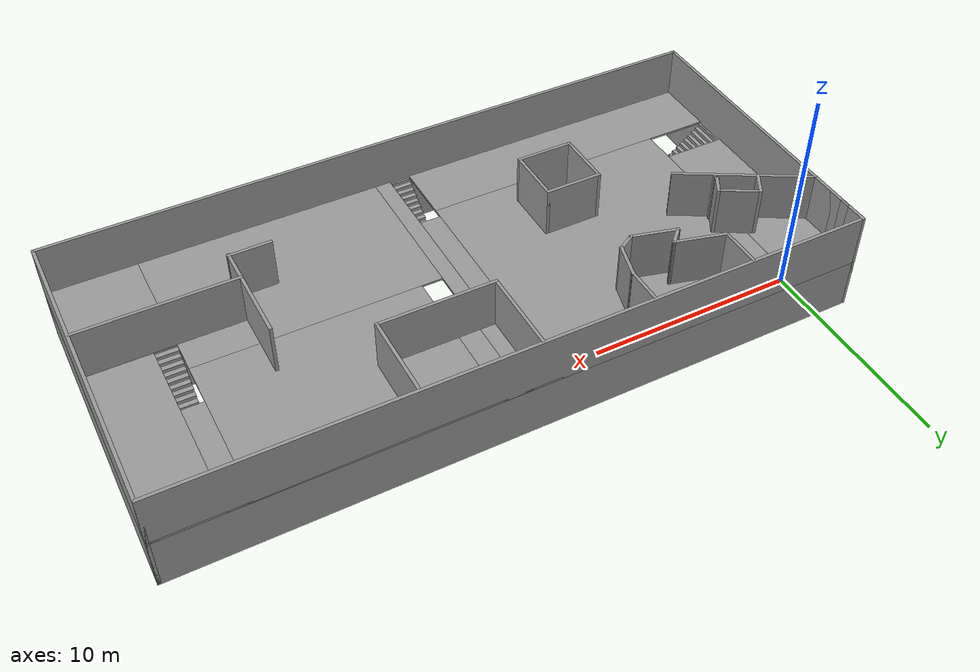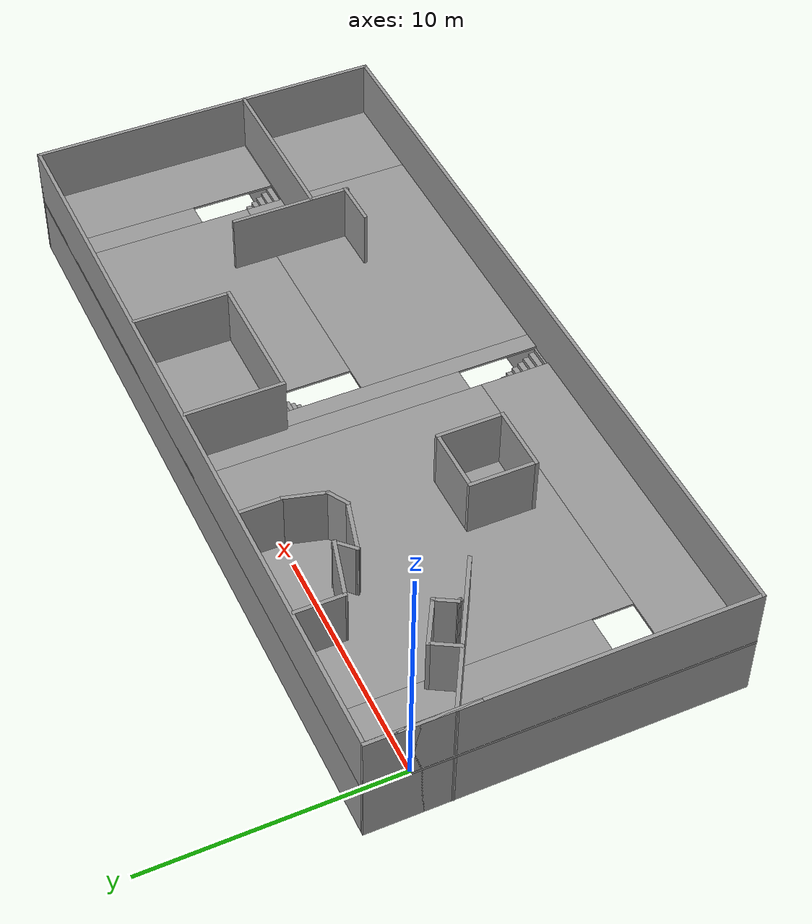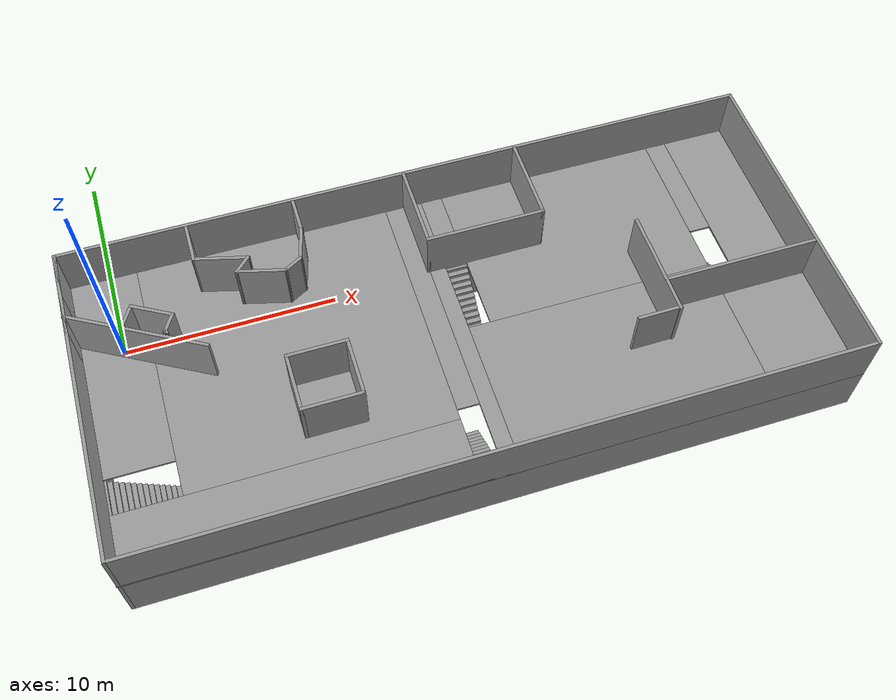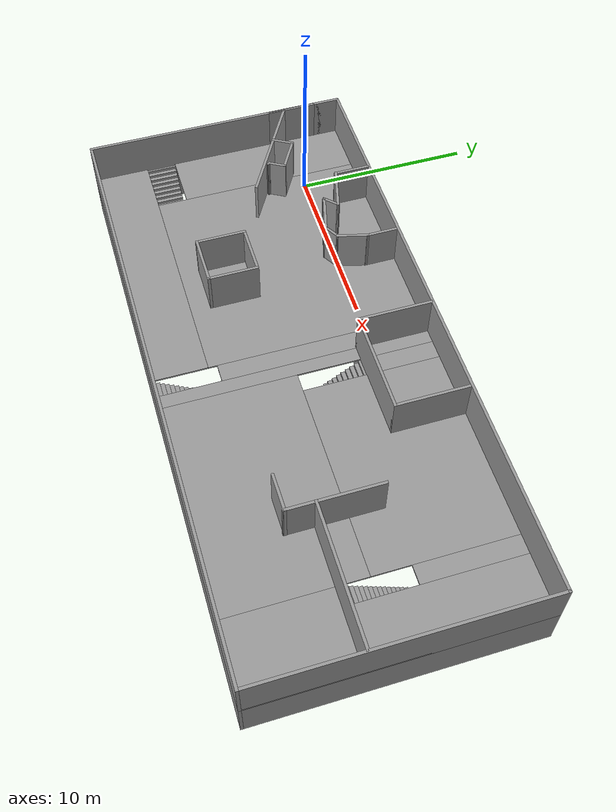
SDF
<?xml version='1.0'?>
<sdf version='1.7'>
  <model name='room_with_stairs'>
    <pose>14.4599 -4.86742 0 0 -0 0</pose>
    <link name='Floor_0'>
      <pose>-1e-06 0 2.5 0 -0 0</pose>
      <visual name='Floor_0_Visual_0'>
        <pose>-16.1009 0 0.05 0 -0 0</pose>
        <geometry>
          <box>
            <size>0.075725 14.75 0.1</size>
          </box>
        </geometry>
        <material>
          <script>
            <uri>file://media/materials/scripts/gazebo.material</uri>
            <name>Gazebo/Grey</name>
          </script>
          <ambient>1 1 1 1</ambient>
        </material>
        <meta>
          <layer>1</layer>
        </meta>
      </visual>
      <collision name='Floor_0_Collision_0'>
        <geometry>
          <box>
            <size>0.075725 14.75 0.1</size>
          </box>
        </geometry>
        <pose>-16.1009 0 0.05 0 -0 0</pose>
      </collision>
      <visual name='Floor_0_Visual_1'>
        <pose>0.183693 0 0.05 0 -0 0</pose>
        <geometry>
          <box>
            <size>0.743302 14.75 0.1</size>
          </box>
        </geometry>
        <material>
          <script>
            <uri>file://media/materials/scripts/gazebo.material</uri>
            <name>Gazebo/Grey</name>
          </script>
          <ambient>1 1 1 1</ambient>
        </material>
        <meta>
          <layer>1</layer>
        </meta>
      </visual>
      <collision name='Floor_0_Collision_1'>
        <geometry>
          <box>
            <size>0.743302 14.75 0.1</size>
          </box>
        </geometry>
        <pose>0.183693 0 0.05 0 -0 0</pose>
      </collision>
      <visual name='Floor_0_Visual_2'>
        <pose>-8.62548 -5.85906 0.05 0 -0 0</pose>
        <geometry>
          <box>
            <size>14.875 3.03188 0.1</size>
          </box>
        </geometry>
        <material>
          <script>
            <uri>file://media/materials/scripts/gazebo.material</uri>
            <name>Gazebo/Grey</name>
          </script>
          <ambient>1 1 1 1</ambient>
        </material>
        <meta>
          <layer>1</layer>
        </meta>
      </visual>
      <collision name='Floor_0_Collision_2'>
        <geometry>
          <box>
            <size>14.875 3.03188 0.1</size>
          </box>
        </geometry>
        <pose>-8.62548 -5.85906 0.05 0 -0 0</pose>
      </collision>
      <visual name='Floor_0_Visual_3'>
        <pose>6.30013 -3.74051 0.05 0 -0 0</pose>
        <geometry>
          <box>
            <size>11.4896 7.26898 0.1</size>
          </box>
        </geometry>
        <material>
          <script>
            <uri>file://media/materials/scripts/gazebo.material</uri>
            <name>Gazebo/Grey</name>
          </script>
          <ambient>1 1 1 1</ambient>
        </material>
        <meta>
          <layer>1</layer>
        </meta>
      </visual>
      <collision name='Floor_0_Collision_3'>
        <geometry>
          <box>
            <size>11.4896 7.26898 0.1</size>
          </box>
        </geometry>
        <pose>6.30013 -3.74051 0.05 0 -0 0</pose>
      </collision>
      <visual name='Floor_0_Visual_4'>
        <pose>-0.687958 -7.37454 0.05 0 -0 0</pose>
        <geometry>
          <box>
            <size>1 0.000917 0.1</size>
          </box>
        </geometry>
        <material>
          <script>
            <uri>file://media/materials/scripts/gazebo.material</uri>
            <name>Gazebo/Grey</name>
          </script>
          <ambient>1 1 1 1</ambient>
        </material>
        <meta>
          <layer>1</layer>
        </meta>
      </visual>
      <collision name='Floor_0_Collision_4'>
        <geometry>
          <box>
            <size>1 0.000917 0.1</size>
          </box>
        </geometry>
        <pose>-0.687958 -7.37454 0.05 0 -0 0</pose>
      </collision>
      <visual name='Floor_0_Visual_5'>
        <pose>14.0918 -4.49895 0.05 0 -0 0</pose>
        <geometry>
          <box>
            <size>4.09381 5.7521 0.1</size>
          </box>
        </geometry>
        <material>
          <script>
            <uri>file://media/materials/scripts/gazebo.material</uri>
            <name>Gazebo/Grey</name>
          </script>
          <ambient>1 1 1 1</ambient>
        </material>
        <meta>
          <layer>1</layer>
        </meta>
      </visual>
      <collision name='Floor_0_Collision_5'>
        <geometry>
          <box>
            <size>4.09381 5.7521 0.1</size>
          </box>
        </geometry>
        <pose>14.0918 -4.49895 0.05 0 -0 0</pose>
      </collision>
      <visual name='Floor_0_Visual_6'>
        <pose>-7.07815 1.51594 0.05 0 -0 0</pose>
        <geometry>
          <box>
            <size>11.7804 11.7181 0.1</size>
          </box>
        </geometry>
        <material>
          <script>
            <uri>file://media/materials/scripts/gazebo.material</uri>
            <name>Gazebo/Grey</name>
          </script>
          <ambient>1 1 1 1</ambient>
        </material>
        <meta>
          <layer>1</layer>
        </meta>
      </visual>
      <collision name='Floor_0_Collision_6'>
        <geometry>
          <box>
            <size>11.7804 11.7181 0.1</size>
          </box>
        </geometry>
        <pose>-7.07815 1.51594 0.05 0 -0 0</pose>
      </collision>
      <visual name='Floor_0_Visual_7'>
        <pose>-0.687958 1.75046 0.05 0 -0 0</pose>
        <geometry>
          <box>
            <size>1 11.2491 0.1</size>
          </box>
        </geometry>
        <material>
          <script>
            <uri>file://media/materials/scripts/gazebo.material</uri>
            <name>Gazebo/Grey</name>
          </script>
          <ambient>1 1 1 1</ambient>
        </material>
        <meta>
          <layer>1</layer>
        </meta>
      </visual>
      <collision name='Floor_0_Collision_7'>
        <geometry>
          <box>
            <size>1 11.2491 0.1</size>
          </box>
        </geometry>
        <pose>-0.687958 1.75046 0.05 0 -0 0</pose>
      </collision>
      <visual name='Floor_0_Visual_8'>
        <pose>-14.5157 2.33638 0.05 0 -0 0</pose>
        <geometry>
          <box>
            <size>3.09467 10.0772 0.1</size>
          </box>
        </geometry>
        <material>
          <script>
            <uri>file://media/materials/scripts/gazebo.material</uri>
            <name>Gazebo/Grey</name>
          </script>
          <ambient>1 1 1 1</ambient>
        </material>
        <meta>
          <layer>1</layer>
        </meta>
      </visual>
      <collision name='Floor_0_Collision_8'>
        <geometry>
          <box>
            <size>3.09467 10.0772 0.1</size>
          </box>
        </geometry>
        <pose>-14.5157 2.33638 0.05 0 -0 0</pose>
      </collision>
      <visual name='Floor_0_Visual_9'>
        <pose>14.5918 2.87605 0.05 0 -0 0</pose>
        <geometry>
          <box>
            <size>3.09381 8.9979 0.1</size>
          </box>
        </geometry>
        <material>
          <script>
            <uri>file://media/materials/scripts/gazebo.material</uri>
            <name>Gazebo/Grey</name>
          </script>
          <ambient>1 1 1 1</ambient>
        </material>
        <meta>
          <layer>1</layer>
        </meta>
      </visual>
      <collision name='Floor_0_Collision_9'>
        <geometry>
          <box>
            <size>3.09381 8.9979 0.1</size>
          </box>
        </geometry>
        <pose>14.5918 2.87605 0.05 0 -0 0</pose>
      </collision>
      <visual name='Floor_0_Visual_10'>
        <pose>6.80013 3.63449 0.05 0 -0 0</pose>
        <geometry>
          <box>
            <size>10.4896 7.48102 0.1</size>
          </box>
        </geometry>
        <material>
          <script>
            <uri>file://media/materials/scripts/gazebo.material</uri>
            <name>Gazebo/Grey</name>
          </script>
          <ambient>1 1 1 1</ambient>
        </material>
        <meta>
          <layer>1</layer>
        </meta>
      </visual>
      <collision name='Floor_0_Collision_10'>
        <geometry>
          <box>
            <size>10.4896 7.48102 0.1</size>
          </box>
        </geometry>
        <pose>6.80013 3.63449 0.05 0 -0 0</pose>
      </collision>
      <visual name='Floor_0_Visual_11'>
        <pose>12.5449 4.62605 0.05 0 -0 0</pose>
        <geometry>
          <box>
            <size>1 5.4979 0.1</size>
          </box>
        </geometry>
        <material>
          <script>
            <uri>file://media/materials/scripts/gazebo.material</uri>
            <name>Gazebo/Grey</name>
          </script>
          <ambient>1 1 1 1</ambient>
        </material>
        <meta>
          <layer>1</layer>
        </meta>
      </visual>
      <collision name='Floor_0_Collision_11'>
        <geometry>
          <box>
            <size>1 5.4979 0.1</size>
          </box>
        </geometry>
        <pose>12.5449 4.62605 0.05 0 -0 0</pose>
      </collision>
      <visual name='Floor_0_Visual_12'>
        <pose>1.05534 5.38449 0.05 0 -0 0</pose>
        <geometry>
          <box>
            <size>1 3.98102 0.1</size>
          </box>
        </geometry>
        <material>
          <script>
            <uri>file://media/materials/scripts/gazebo.material</uri>
            <name>Gazebo/Grey</name>
          </script>
          <ambient>1 1 1 1</ambient>
        </material>
        <meta>
          <layer>1</layer>
        </meta>
      </visual>
      <collision name='Floor_0_Collision_12'>
        <geometry>
          <box>
            <size>1 3.98102 0.1</size>
          </box>
        </geometry>
        <pose>1.05534 5.38449 0.05 0 -0 0</pose>
      </collision>
    </link>
    <link name='Stairs_0'>
      <visual name='Stairs_0_Visual_0'>
        <pose>-0.687958 -3.99075 0.083333 0 -0 0</pose>
        <geometry>
          <box>
            <size>1 0.233333 0.166667</size>
          </box>
        </geometry>
        <material>
          <script>
            <uri>file://media/materials/scripts/gazebo.material</uri>
            <name>Gazebo/Grey</name>
          </script>
          <ambient>1 1 1 1</ambient>
        </material>
        <meta>
          <layer>0</layer>
        </meta>
      </visual>
      <collision name='Stairs_0_Collision_0'>
        <geometry>
          <box>
            <size>1 0.233333 0.166667</size>
          </box>
        </geometry>
        <pose>-0.687958 -3.99075 0.083333 0 -0 0</pose>
      </collision>
      <visual name='Stairs_0_Visual_1'>
        <pose>-0.687958 -4.22408 0.25 0 -0 0</pose>
        <geometry>
          <box>
            <size>1 0.233333 0.166667</size>
          </box>
        </geometry>
        <material>
          <script>
            <uri>file://media/materials/scripts/gazebo.material</uri>
            <name>Gazebo/Grey</name>
          </script>
          <ambient>1 1 1 1</ambient>
        </material>
        <meta>
          <layer>0</layer>
        </meta>
      </visual>
      <collision name='Stairs_0_Collision_1'>
        <geometry>
          <box>
            <size>1 0.233333 0.166667</size>
          </box>
        </geometry>
        <pose>-0.687958 -4.22408 0.25 0 -0 0</pose>
      </collision>
      <visual name='Stairs_0_Visual_2'>
        <pose>-0.687958 -4.45742 0.416667 0 -0 0</pose>
        <geometry>
          <box>
            <size>1 0.233333 0.166667</size>
          </box>
        </geometry>
        <material>
          <script>
            <uri>file://media/materials/scripts/gazebo.material</uri>
            <name>Gazebo/Grey</name>
          </script>
          <ambient>1 1 1 1</ambient>
        </material>
        <meta>
          <layer>0</layer>
        </meta>
      </visual>
      <collision name='Stairs_0_Collision_2'>
        <geometry>
          <box>
            <size>1 0.233333 0.166667</size>
          </box>
        </geometry>
        <pose>-0.687958 -4.45742 0.416667 0 -0 0</pose>
      </collision>
      <visual name='Stairs_0_Visual_3'>
        <pose>-0.687958 -4.69075 0.583333 0 -0 0</pose>
        <geometry>
          <box>
            <size>1 0.233333 0.166667</size>
          </box>
        </geometry>
        <material>
          <script>
            <uri>file://media/materials/scripts/gazebo.material</uri>
            <name>Gazebo/Grey</name>
          </script>
          <ambient>1 1 1 1</ambient>
        </material>
        <meta>
          <layer>0</layer>
        </meta>
      </visual>
      <collision name='Stairs_0_Collision_3'>
        <geometry>
          <box>
            <size>1 0.233333 0.166667</size>
          </box>
        </geometry>
        <pose>-0.687958 -4.69075 0.583333 0 -0 0</pose>
      </collision>
      <visual name='Stairs_0_Visual_4'>
        <pose>-0.687958 -4.92408 0.75 0 -0 0</pose>
        <geometry>
          <box>
            <size>1 0.233333 0.166667</size>
          </box>
        </geometry>
        <material>
          <script>
            <uri>file://media/materials/scripts/gazebo.material</uri>
            <name>Gazebo/Grey</name>
          </script>
          <ambient>1 1 1 1</ambient>
        </material>
        <meta>
          <layer>0</layer>
        </meta>
      </visual>
      <collision name='Stairs_0_Collision_4'>
        <geometry>
          <box>
            <size>1 0.233333 0.166667</size>
          </box>
        </geometry>
        <pose>-0.687958 -4.92408 0.75 0 -0 0</pose>
      </collision>
      <visual name='Stairs_0_Visual_5'>
        <pose>-0.687958 -5.15742 0.916667 0 -0 0</pose>
        <geometry>
          <box>
            <size>1 0.233333 0.166667</size>
          </box>
        </geometry>
        <material>
          <script>
            <uri>file://media/materials/scripts/gazebo.material</uri>
            <name>Gazebo/Grey</name>
          </script>
          <ambient>1 1 1 1</ambient>
        </material>
        <meta>
          <layer>0</layer>
        </meta>
      </visual>
      <collision name='Stairs_0_Collision_5'>
        <geometry>
          <box>
            <size>1 0.233333 0.166667</size>
          </box>
        </geometry>
        <pose>-0.687958 -5.15742 0.916667 0 -0 0</pose>
      </collision>
      <visual name='Stairs_0_Visual_6'>
        <pose>-0.687958 -5.39075 1.08333 0 -0 0</pose>
        <geometry>
          <box>
            <size>1 0.233333 0.166667</size>
          </box>
        </geometry>
        <material>
          <script>
            <uri>file://media/materials/scripts/gazebo.material</uri>
            <name>Gazebo/Grey</name>
          </script>
          <ambient>1 1 1 1</ambient>
        </material>
        <meta>
          <layer>0</layer>
        </meta>
      </visual>
      <collision name='Stairs_0_Collision_6'>
        <geometry>
          <box>
            <size>1 0.233333 0.166667</size>
          </box>
        </geometry>
        <pose>-0.687958 -5.39075 1.08333 0 -0 0</pose>
      </collision>
      <visual name='Stairs_0_Visual_7'>
        <pose>-0.687958 -5.62408 1.25 0 -0 0</pose>
        <geometry>
          <box>
            <size>1 0.233333 0.166667</size>
          </box>
        </geometry>
        <material>
          <script>
            <uri>file://media/materials/scripts/gazebo.material</uri>
            <name>Gazebo/Grey</name>
          </script>
          <ambient>1 1 1 1</ambient>
        </material>
        <meta>
          <layer>0</layer>
        </meta>
      </visual>
      <collision name='Stairs_0_Collision_7'>
        <geometry>
          <box>
            <size>1 0.233333 0.166667</size>
          </box>
        </geometry>
        <pose>-0.687958 -5.62408 1.25 0 -0 0</pose>
      </collision>
      <visual name='Stairs_0_Visual_8'>
        <pose>-0.687958 -5.85742 1.41667 0 -0 0</pose>
        <geometry>
          <box>
            <size>1 0.233333 0.166667</size>
          </box>
        </geometry>
        <material>
          <script>
            <uri>file://media/materials/scripts/gazebo.material</uri>
            <name>Gazebo/Grey</name>
          </script>
          <ambient>1 1 1 1</ambient>
        </material>
        <meta>
          <layer>0</layer>
        </meta>
      </visual>
      <collision name='Stairs_0_Collision_8'>
        <geometry>
          <box>
            <size>1 0.233333 0.166667</size>
          </box>
        </geometry>
        <pose>-0.687958 -5.85742 1.41667 0 -0 0</pose>
      </collision>
      <visual name='Stairs_0_Visual_9'>
        <pose>-0.687958 -6.09075 1.58333 0 -0 0</pose>
        <geometry>
          <box>
            <size>1 0.233333 0.166667</size>
          </box>
        </geometry>
        <material>
          <script>
            <uri>file://media/materials/scripts/gazebo.material</uri>
            <name>Gazebo/Grey</name>
          </script>
          <ambient>1 1 1 1</ambient>
        </material>
        <meta>
          <layer>0</layer>
        </meta>
      </visual>
      <collision name='Stairs_0_Collision_9'>
        <geometry>
          <box>
            <size>1 0.233333 0.166667</size>
          </box>
        </geometry>
        <pose>-0.687958 -6.09075 1.58333 0 -0 0</pose>
      </collision>
      <visual name='Stairs_0_Visual_10'>
        <pose>-0.687958 -6.32408 1.75 0 -0 0</pose>
        <geometry>
          <box>
            <size>1 0.233333 0.166667</size>
          </box>
        </geometry>
        <material>
          <script>
            <uri>file://media/materials/scripts/gazebo.material</uri>
            <name>Gazebo/Grey</name>
          </script>
          <ambient>1 1 1 1</ambient>
        </material>
        <meta>
          <layer>0</layer>
        </meta>
      </visual>
      <collision name='Stairs_0_Collision_10'>
        <geometry>
          <box>
            <size>1 0.233333 0.166667</size>
          </box>
        </geometry>
        <pose>-0.687958 -6.32408 1.75 0 -0 0</pose>
      </collision>
      <visual name='Stairs_0_Visual_11'>
        <pose>-0.687958 -6.55742 1.91667 0 -0 0</pose>
        <geometry>
          <box>
            <size>1 0.233333 0.166667</size>
          </box>
        </geometry>
        <material>
          <script>
            <uri>file://media/materials/scripts/gazebo.material</uri>
            <name>Gazebo/Grey</name>
          </script>
          <ambient>1 1 1 1</ambient>
        </material>
        <meta>
          <layer>0</layer>
        </meta>
      </visual>
      <collision name='Stairs_0_Collision_11'>
        <geometry>
          <box>
            <size>1 0.233333 0.166667</size>
          </box>
        </geometry>
        <pose>-0.687958 -6.55742 1.91667 0 -0 0</pose>
      </collision>
      <visual name='Stairs_0_Visual_12'>
        <pose>-0.687958 -6.79075 2.08333 0 -0 0</pose>
        <geometry>
          <box>
            <size>1 0.233333 0.166667</size>
          </box>
        </geometry>
        <material>
          <script>
            <uri>file://media/materials/scripts/gazebo.material</uri>
            <name>Gazebo/Grey</name>
          </script>
          <ambient>1 1 1 1</ambient>
        </material>
        <meta>
          <layer>0</layer>
        </meta>
      </visual>
      <collision name='Stairs_0_Collision_12'>
        <geometry>
          <box>
            <size>1 0.233333 0.166667</size>
          </box>
        </geometry>
        <pose>-0.687958 -6.79075 2.08333 0 -0 0</pose>
      </collision>
      <visual name='Stairs_0_Visual_13'>
        <pose>-0.687958 -7.02408 2.25 0 -0 0</pose>
        <geometry>
          <box>
            <size>1 0.233333 0.166667</size>
          </box>
        </geometry>
        <material>
          <script>
            <uri>file://media/materials/scripts/gazebo.material</uri>
            <name>Gazebo/Grey</name>
          </script>
          <ambient>1 1 1 1</ambient>
        </material>
        <meta>
          <layer>0</layer>
        </meta>
      </visual>
      <collision name='Stairs_0_Collision_13'>
        <geometry>
          <box>
            <size>1 0.233333 0.166667</size>
          </box>
        </geometry>
        <pose>-0.687958 -7.02408 2.25 0 -0 0</pose>
      </collision>
      <visual name='Stairs_0_Visual_14'>
        <pose>-0.687958 -7.25742 2.41667 0 -0 0</pose>
        <geometry>
          <box>
            <size>1 0.233333 0.166667</size>
          </box>
        </geometry>
        <material>
          <script>
            <uri>file://media/materials/scripts/gazebo.material</uri>
            <name>Gazebo/Grey</name>
          </script>
          <ambient>1 1 1 1</ambient>
        </material>
        <meta>
          <layer>0</layer>
        </meta>
      </visual>
      <collision name='Stairs_0_Collision_14'>
        <geometry>
          <box>
            <size>1 0.233333 0.166667</size>
          </box>
        </geometry>
        <pose>-0.687958 -7.25742 2.41667 0 -0 0</pose>
      </collision>
    </link>
    <link name='Stairs_1'>
      <visual name='Stairs_1_Visual_0'>
        <pose>-13.0715 -3.52268 0.083333 0 -0 -1.5708</pose>
        <geometry>
          <box>
            <size>1.64089 0.206311 0.166667</size>
          </box>
        </geometry>
        <material>
          <script>
            <uri>file://media/materials/scripts/gazebo.material</uri>
            <name>Gazebo/Grey</name>
          </script>
          <ambient>1 1 1 1</ambient>
        </material>
        <meta>
          <layer>0</layer>
        </meta>
      </visual>
      <collision name='Stairs_1_Collision_0'>
        <geometry>
          <box>
            <size>1.64089 0.206311 0.166667</size>
          </box>
        </geometry>
        <pose>-13.0715 -3.52268 0.083333 0 -0 -1.5708</pose>
      </collision>
      <visual name='Stairs_1_Visual_1'>
        <pose>-13.2778 -3.52268 0.25 0 -0 -1.5708</pose>
        <geometry>
          <box>
            <size>1.64089 0.206311 0.166667</size>
          </box>
        </geometry>
        <material>
          <script>
            <uri>file://media/materials/scripts/gazebo.material</uri>
            <name>Gazebo/Grey</name>
          </script>
          <ambient>1 1 1 1</ambient>
        </material>
        <meta>
          <layer>0</layer>
        </meta>
      </visual>
      <collision name='Stairs_1_Collision_1'>
        <geometry>
          <box>
            <size>1.64089 0.206311 0.166667</size>
          </box>
        </geometry>
        <pose>-13.2778 -3.52268 0.25 0 -0 -1.5708</pose>
      </collision>
      <visual name='Stairs_1_Visual_2'>
        <pose>-13.4841 -3.52268 0.416667 0 -0 -1.5708</pose>
        <geometry>
          <box>
            <size>1.64089 0.206311 0.166667</size>
          </box>
        </geometry>
        <material>
          <script>
            <uri>file://media/materials/scripts/gazebo.material</uri>
            <name>Gazebo/Grey</name>
          </script>
          <ambient>1 1 1 1</ambient>
        </material>
        <meta>
          <layer>0</layer>
        </meta>
      </visual>
      <collision name='Stairs_1_Collision_2'>
        <geometry>
          <box>
            <size>1.64089 0.206311 0.166667</size>
          </box>
        </geometry>
        <pose>-13.4841 -3.52268 0.416667 0 -0 -1.5708</pose>
      </collision>
      <visual name='Stairs_1_Visual_3'>
        <pose>-13.6904 -3.52268 0.583333 0 -0 -1.5708</pose>
        <geometry>
          <box>
            <size>1.64089 0.206311 0.166667</size>
          </box>
        </geometry>
        <material>
          <script>
            <uri>file://media/materials/scripts/gazebo.material</uri>
            <name>Gazebo/Grey</name>
          </script>
          <ambient>1 1 1 1</ambient>
        </material>
        <meta>
          <layer>0</layer>
        </meta>
      </visual>
      <collision name='Stairs_1_Collision_3'>
        <geometry>
          <box>
            <size>1.64089 0.206311 0.166667</size>
          </box>
        </geometry>
        <pose>-13.6904 -3.52268 0.583333 0 -0 -1.5708</pose>
      </collision>
      <visual name='Stairs_1_Visual_4'>
        <pose>-13.8967 -3.52268 0.75 0 -0 -1.5708</pose>
        <geometry>
          <box>
            <size>1.64089 0.206311 0.166667</size>
          </box>
        </geometry>
        <material>
          <script>
            <uri>file://media/materials/scripts/gazebo.material</uri>
            <name>Gazebo/Grey</name>
          </script>
          <ambient>1 1 1 1</ambient>
        </material>
        <meta>
          <layer>0</layer>
        </meta>
      </visual>
      <collision name='Stairs_1_Collision_4'>
        <geometry>
          <box>
            <size>1.64089 0.206311 0.166667</size>
          </box>
        </geometry>
        <pose>-13.8967 -3.52268 0.75 0 -0 -1.5708</pose>
      </collision>
      <visual name='Stairs_1_Visual_5'>
        <pose>-14.103 -3.52268 0.916667 0 -0 -1.5708</pose>
        <geometry>
          <box>
            <size>1.64089 0.206311 0.166667</size>
          </box>
        </geometry>
        <material>
          <script>
            <uri>file://media/materials/scripts/gazebo.material</uri>
            <name>Gazebo/Grey</name>
          </script>
          <ambient>1 1 1 1</ambient>
        </material>
        <meta>
          <layer>0</layer>
        </meta>
      </visual>
      <collision name='Stairs_1_Collision_5'>
        <geometry>
          <box>
            <size>1.64089 0.206311 0.166667</size>
          </box>
        </geometry>
        <pose>-14.103 -3.52268 0.916667 0 -0 -1.5708</pose>
      </collision>
      <visual name='Stairs_1_Visual_6'>
        <pose>-14.3094 -3.52268 1.08333 0 -0 -1.5708</pose>
        <geometry>
          <box>
            <size>1.64089 0.206311 0.166667</size>
          </box>
        </geometry>
        <material>
          <script>
            <uri>file://media/materials/scripts/gazebo.material</uri>
            <name>Gazebo/Grey</name>
          </script>
          <ambient>1 1 1 1</ambient>
        </material>
        <meta>
          <layer>0</layer>
        </meta>
      </visual>
      <collision name='Stairs_1_Collision_6'>
        <geometry>
          <box>
            <size>1.64089 0.206311 0.166667</size>
          </box>
        </geometry>
        <pose>-14.3094 -3.52268 1.08333 0 -0 -1.5708</pose>
      </collision>
      <visual name='Stairs_1_Visual_7'>
        <pose>-14.5157 -3.52268 1.25 0 -0 -1.5708</pose>
        <geometry>
          <box>
            <size>1.64089 0.206311 0.166667</size>
          </box>
        </geometry>
        <material>
          <script>
            <uri>file://media/materials/scripts/gazebo.material</uri>
            <name>Gazebo/Grey</name>
          </script>
          <ambient>1 1 1 1</ambient>
        </material>
        <meta>
          <layer>0</layer>
        </meta>
      </visual>
      <collision name='Stairs_1_Collision_7'>
        <geometry>
          <box>
            <size>1.64089 0.206311 0.166667</size>
          </box>
        </geometry>
        <pose>-14.5157 -3.52268 1.25 0 -0 -1.5708</pose>
      </collision>
      <visual name='Stairs_1_Visual_8'>
        <pose>-14.722 -3.52268 1.41667 0 -0 -1.5708</pose>
        <geometry>
          <box>
            <size>1.64089 0.206311 0.166667</size>
          </box>
        </geometry>
        <material>
          <script>
            <uri>file://media/materials/scripts/gazebo.material</uri>
            <name>Gazebo/Grey</name>
          </script>
          <ambient>1 1 1 1</ambient>
        </material>
        <meta>
          <layer>0</layer>
        </meta>
      </visual>
      <collision name='Stairs_1_Collision_8'>
        <geometry>
          <box>
            <size>1.64089 0.206311 0.166667</size>
          </box>
        </geometry>
        <pose>-14.722 -3.52268 1.41667 0 -0 -1.5708</pose>
      </collision>
      <visual name='Stairs_1_Visual_9'>
        <pose>-14.9283 -3.52268 1.58333 0 -0 -1.5708</pose>
        <geometry>
          <box>
            <size>1.64089 0.206311 0.166667</size>
          </box>
        </geometry>
        <material>
          <script>
            <uri>file://media/materials/scripts/gazebo.material</uri>
            <name>Gazebo/Grey</name>
          </script>
          <ambient>1 1 1 1</ambient>
        </material>
        <meta>
          <layer>0</layer>
        </meta>
      </visual>
      <collision name='Stairs_1_Collision_9'>
        <geometry>
          <box>
            <size>1.64089 0.206311 0.166667</size>
          </box>
        </geometry>
        <pose>-14.9283 -3.52268 1.58333 0 -0 -1.5708</pose>
      </collision>
      <visual name='Stairs_1_Visual_10'>
        <pose>-15.1346 -3.52268 1.75 0 -0 -1.5708</pose>
        <geometry>
          <box>
            <size>1.64089 0.206311 0.166667</size>
          </box>
        </geometry>
        <material>
          <script>
            <uri>file://media/materials/scripts/gazebo.material</uri>
            <name>Gazebo/Grey</name>
          </script>
          <ambient>1 1 1 1</ambient>
        </material>
        <meta>
          <layer>0</layer>
        </meta>
      </visual>
      <collision name='Stairs_1_Collision_10'>
        <geometry>
          <box>
            <size>1.64089 0.206311 0.166667</size>
          </box>
        </geometry>
        <pose>-15.1346 -3.52268 1.75 0 -0 -1.5708</pose>
      </collision>
      <visual name='Stairs_1_Visual_11'>
        <pose>-15.3409 -3.52268 1.91667 0 -0 -1.5708</pose>
        <geometry>
          <box>
            <size>1.64089 0.206311 0.166667</size>
          </box>
        </geometry>
        <material>
          <script>
            <uri>file://media/materials/scripts/gazebo.material</uri>
            <name>Gazebo/Grey</name>
          </script>
          <ambient>1 1 1 1</ambient>
        </material>
        <meta>
          <layer>0</layer>
        </meta>
      </visual>
      <collision name='Stairs_1_Collision_11'>
        <geometry>
          <box>
            <size>1.64089 0.206311 0.166667</size>
          </box>
        </geometry>
        <pose>-15.3409 -3.52268 1.91667 0 -0 -1.5708</pose>
      </collision>
      <visual name='Stairs_1_Visual_12'>
        <pose>-15.5472 -3.52268 2.08333 0 -0 -1.5708</pose>
        <geometry>
          <box>
            <size>1.64089 0.206311 0.166667</size>
          </box>
        </geometry>
        <material>
          <script>
            <uri>file://media/materials/scripts/gazebo.material</uri>
            <name>Gazebo/Grey</name>
          </script>
          <ambient>1 1 1 1</ambient>
        </material>
        <meta>
          <layer>0</layer>
        </meta>
      </visual>
      <collision name='Stairs_1_Collision_12'>
        <geometry>
          <box>
            <size>1.64089 0.206311 0.166667</size>
          </box>
        </geometry>
        <pose>-15.5472 -3.52268 2.08333 0 -0 -1.5708</pose>
      </collision>
      <visual name='Stairs_1_Visual_13'>
        <pose>-15.7535 -3.52268 2.25 0 -0 -1.5708</pose>
        <geometry>
          <box>
            <size>1.64089 0.206311 0.166667</size>
          </box>
        </geometry>
        <material>
          <script>
            <uri>file://media/materials/scripts/gazebo.material</uri>
            <name>Gazebo/Grey</name>
          </script>
          <ambient>1 1 1 1</ambient>
        </material>
        <meta>
          <layer>0</layer>
        </meta>
      </visual>
      <collision name='Stairs_1_Collision_13'>
        <geometry>
          <box>
            <size>1.64089 0.206311 0.166667</size>
          </box>
        </geometry>
        <pose>-15.7535 -3.52268 2.25 0 -0 -1.5708</pose>
      </collision>
      <visual name='Stairs_1_Visual_14'>
        <pose>-15.9598 -3.52268 2.41667 0 -0 -1.5708</pose>
        <geometry>
          <box>
            <size>1.64089 0.206311 0.166667</size>
          </box>
        </geometry>
        <material>
          <script>
            <uri>file://media/materials/scripts/gazebo.material</uri>
            <name>Gazebo/Grey</name>
          </script>
          <ambient>1 1 1 1</ambient>
        </material>
        <meta>
          <layer>0</layer>
        </meta>
      </visual>
      <collision name='Stairs_1_Collision_14'>
        <geometry>
          <box>
            <size>1.64089 0.206311 0.166667</size>
          </box>
        </geometry>
        <pose>-15.9598 -3.52268 2.41667 0 -0 -1.5708</pose>
      </collision>
    </link>
    <link name='Stairs_2'>
      <visual name='Stairs_2_Visual_0'>
        <pose>1.05534 0.01065 0.083333 0 -0 -3.14159</pose>
        <geometry>
          <box>
            <size>1 0.233333 0.166667</size>
          </box>
        </geometry>
        <material>
          <script>
            <uri>file://media/materials/scripts/gazebo.material</uri>
            <name>Gazebo/Grey</name>
          </script>
          <ambient>1 1 1 1</ambient>
        </material>
        <meta>
          <layer>0</layer>
        </meta>
      </visual>
      <collision name='Stairs_2_Collision_0'>
        <geometry>
          <box>
            <size>1 0.233333 0.166667</size>
          </box>
        </geometry>
        <pose>1.05534 0.01065 0.083333 0 -0 -3.14159</pose>
      </collision>
      <visual name='Stairs_2_Visual_1'>
        <pose>1.05534 0.243983 0.25 0 -0 -3.14159</pose>
        <geometry>
          <box>
            <size>1 0.233333 0.166667</size>
          </box>
        </geometry>
        <material>
          <script>
            <uri>file://media/materials/scripts/gazebo.material</uri>
            <name>Gazebo/Grey</name>
          </script>
          <ambient>1 1 1 1</ambient>
        </material>
        <meta>
          <layer>0</layer>
        </meta>
      </visual>
      <collision name='Stairs_2_Collision_1'>
        <geometry>
          <box>
            <size>1 0.233333 0.166667</size>
          </box>
        </geometry>
        <pose>1.05534 0.243983 0.25 0 -0 -3.14159</pose>
      </collision>
      <visual name='Stairs_2_Visual_2'>
        <pose>1.05534 0.477316 0.416667 0 -0 -3.14159</pose>
        <geometry>
          <box>
            <size>1 0.233333 0.166667</size>
          </box>
        </geometry>
        <material>
          <script>
            <uri>file://media/materials/scripts/gazebo.material</uri>
            <name>Gazebo/Grey</name>
          </script>
          <ambient>1 1 1 1</ambient>
        </material>
        <meta>
          <layer>0</layer>
        </meta>
      </visual>
      <collision name='Stairs_2_Collision_2'>
        <geometry>
          <box>
            <size>1 0.233333 0.166667</size>
          </box>
        </geometry>
        <pose>1.05534 0.477316 0.416667 0 -0 -3.14159</pose>
      </collision>
      <visual name='Stairs_2_Visual_3'>
        <pose>1.05534 0.710649 0.583333 0 -0 -3.14159</pose>
        <geometry>
          <box>
            <size>1 0.233333 0.166667</size>
          </box>
        </geometry>
        <material>
          <script>
            <uri>file://media/materials/scripts/gazebo.material</uri>
            <name>Gazebo/Grey</name>
          </script>
          <ambient>1 1 1 1</ambient>
        </material>
        <meta>
          <layer>0</layer>
        </meta>
      </visual>
      <collision name='Stairs_2_Collision_3'>
        <geometry>
          <box>
            <size>1 0.233333 0.166667</size>
          </box>
        </geometry>
        <pose>1.05534 0.710649 0.583333 0 -0 -3.14159</pose>
      </collision>
      <visual name='Stairs_2_Visual_4'>
        <pose>1.05534 0.943983 0.75 0 -0 -3.14159</pose>
        <geometry>
          <box>
            <size>1 0.233333 0.166667</size>
          </box>
        </geometry>
        <material>
          <script>
            <uri>file://media/materials/scripts/gazebo.material</uri>
            <name>Gazebo/Grey</name>
          </script>
          <ambient>1 1 1 1</ambient>
        </material>
        <meta>
          <layer>0</layer>
        </meta>
      </visual>
      <collision name='Stairs_2_Collision_4'>
        <geometry>
          <box>
            <size>1 0.233333 0.166667</size>
          </box>
        </geometry>
        <pose>1.05534 0.943983 0.75 0 -0 -3.14159</pose>
      </collision>
      <visual name='Stairs_2_Visual_5'>
        <pose>1.05534 1.17732 0.916667 0 -0 -3.14159</pose>
        <geometry>
          <box>
            <size>1 0.233333 0.166667</size>
          </box>
        </geometry>
        <material>
          <script>
            <uri>file://media/materials/scripts/gazebo.material</uri>
            <name>Gazebo/Grey</name>
          </script>
          <ambient>1 1 1 1</ambient>
        </material>
        <meta>
          <layer>0</layer>
        </meta>
      </visual>
      <collision name='Stairs_2_Collision_5'>
        <geometry>
          <box>
            <size>1 0.233333 0.166667</size>
          </box>
        </geometry>
        <pose>1.05534 1.17732 0.916667 0 -0 -3.14159</pose>
      </collision>
      <visual name='Stairs_2_Visual_6'>
        <pose>1.05534 1.41065 1.08333 0 -0 -3.14159</pose>
        <geometry>
          <box>
            <size>1 0.233333 0.166667</size>
          </box>
        </geometry>
        <material>
          <script>
            <uri>file://media/materials/scripts/gazebo.material</uri>
            <name>Gazebo/Grey</name>
          </script>
          <ambient>1 1 1 1</ambient>
        </material>
        <meta>
          <layer>0</layer>
        </meta>
      </visual>
      <collision name='Stairs_2_Collision_6'>
        <geometry>
          <box>
            <size>1 0.233333 0.166667</size>
          </box>
        </geometry>
        <pose>1.05534 1.41065 1.08333 0 -0 -3.14159</pose>
      </collision>
      <visual name='Stairs_2_Visual_7'>
        <pose>1.05534 1.64398 1.25 0 -0 -3.14159</pose>
        <geometry>
          <box>
            <size>1 0.233333 0.166667</size>
          </box>
        </geometry>
        <material>
          <script>
            <uri>file://media/materials/scripts/gazebo.material</uri>
            <name>Gazebo/Grey</name>
          </script>
          <ambient>1 1 1 1</ambient>
        </material>
        <meta>
          <layer>0</layer>
        </meta>
      </visual>
      <collision name='Stairs_2_Collision_7'>
        <geometry>
          <box>
            <size>1 0.233333 0.166667</size>
          </box>
        </geometry>
        <pose>1.05534 1.64398 1.25 0 -0 -3.14159</pose>
      </collision>
      <visual name='Stairs_2_Visual_8'>
        <pose>1.05534 1.87732 1.41667 0 -0 -3.14159</pose>
        <geometry>
          <box>
            <size>1 0.233333 0.166667</size>
          </box>
        </geometry>
        <material>
          <script>
            <uri>file://media/materials/scripts/gazebo.material</uri>
            <name>Gazebo/Grey</name>
          </script>
          <ambient>1 1 1 1</ambient>
        </material>
        <meta>
          <layer>0</layer>
        </meta>
      </visual>
      <collision name='Stairs_2_Collision_8'>
        <geometry>
          <box>
            <size>1 0.233333 0.166667</size>
          </box>
        </geometry>
        <pose>1.05534 1.87732 1.41667 0 -0 -3.14159</pose>
      </collision>
      <visual name='Stairs_2_Visual_9'>
        <pose>1.05534 2.11065 1.58333 0 -0 -3.14159</pose>
        <geometry>
          <box>
            <size>1 0.233333 0.166667</size>
          </box>
        </geometry>
        <material>
          <script>
            <uri>file://media/materials/scripts/gazebo.material</uri>
            <name>Gazebo/Grey</name>
          </script>
          <ambient>1 1 1 1</ambient>
        </material>
        <meta>
          <layer>0</layer>
        </meta>
      </visual>
      <collision name='Stairs_2_Collision_9'>
        <geometry>
          <box>
            <size>1 0.233333 0.166667</size>
          </box>
        </geometry>
        <pose>1.05534 2.11065 1.58333 0 -0 -3.14159</pose>
      </collision>
      <visual name='Stairs_2_Visual_10'>
        <pose>1.05534 2.34398 1.75 0 -0 -3.14159</pose>
        <geometry>
          <box>
            <size>1 0.233333 0.166667</size>
          </box>
        </geometry>
        <material>
          <script>
            <uri>file://media/materials/scripts/gazebo.material</uri>
            <name>Gazebo/Grey</name>
          </script>
          <ambient>1 1 1 1</ambient>
        </material>
        <meta>
          <layer>0</layer>
        </meta>
      </visual>
      <collision name='Stairs_2_Collision_10'>
        <geometry>
          <box>
            <size>1 0.233333 0.166667</size>
          </box>
        </geometry>
        <pose>1.05534 2.34398 1.75 0 -0 -3.14159</pose>
      </collision>
      <visual name='Stairs_2_Visual_11'>
        <pose>1.05534 2.57732 1.91667 0 -0 -3.14159</pose>
        <geometry>
          <box>
            <size>1 0.233333 0.166667</size>
          </box>
        </geometry>
        <material>
          <script>
            <uri>file://media/materials/scripts/gazebo.material</uri>
            <name>Gazebo/Grey</name>
          </script>
          <ambient>1 1 1 1</ambient>
        </material>
        <meta>
          <layer>0</layer>
        </meta>
      </visual>
      <collision name='Stairs_2_Collision_11'>
        <geometry>
          <box>
            <size>1 0.233333 0.166667</size>
          </box>
        </geometry>
        <pose>1.05534 2.57732 1.91667 0 -0 -3.14159</pose>
      </collision>
      <visual name='Stairs_2_Visual_12'>
        <pose>1.05534 2.81065 2.08333 0 -0 -3.14159</pose>
        <geometry>
          <box>
            <size>1 0.233333 0.166667</size>
          </box>
        </geometry>
        <material>
          <script>
            <uri>file://media/materials/scripts/gazebo.material</uri>
            <name>Gazebo/Grey</name>
          </script>
          <ambient>1 1 1 1</ambient>
        </material>
        <meta>
          <layer>0</layer>
        </meta>
      </visual>
      <collision name='Stairs_2_Collision_12'>
        <geometry>
          <box>
            <size>1 0.233333 0.166667</size>
          </box>
        </geometry>
        <pose>1.05534 2.81065 2.08333 0 -0 -3.14159</pose>
      </collision>
      <visual name='Stairs_2_Visual_13'>
        <pose>1.05534 3.04398 2.25 0 -0 -3.14159</pose>
        <geometry>
          <box>
            <size>1 0.233333 0.166667</size>
          </box>
        </geometry>
        <material>
          <script>
            <uri>file://media/materials/scripts/gazebo.material</uri>
            <name>Gazebo/Grey</name>
          </script>
          <ambient>1 1 1 1</ambient>
        </material>
        <meta>
          <layer>0</layer>
        </meta>
      </visual>
      <collision name='Stairs_2_Collision_13'>
        <geometry>
          <box>
            <size>1 0.233333 0.166667</size>
          </box>
        </geometry>
        <pose>1.05534 3.04398 2.25 0 -0 -3.14159</pose>
      </collision>
      <visual name='Stairs_2_Visual_14'>
        <pose>1.05534 3.27732 2.41667 0 -0 -3.14159</pose>
        <geometry>
          <box>
            <size>1 0.233333 0.166667</size>
          </box>
        </geometry>
        <material>
          <script>
            <uri>file://media/materials/scripts/gazebo.material</uri>
            <name>Gazebo/Grey</name>
          </script>
          <ambient>1 1 1 1</ambient>
        </material>
        <meta>
          <layer>0</layer>
        </meta>
      </visual>
      <collision name='Stairs_2_Collision_14'>
        <geometry>
          <box>
            <size>1 0.233333 0.166667</size>
          </box>
        </geometry>
        <pose>1.05534 3.27732 2.41667 0 -0 -3.14159</pose>
      </collision>
    </link>
    <link name='Stairs_3'>
      <visual name='Stairs_3_Visual_0'>
        <pose>12.5449 1.76044 0.083333 0 -0 0</pose>
        <geometry>
          <box>
            <size>1 0.233333 0.166667</size>
          </box>
        </geometry>
        <material>
          <script>
            <uri>file://media/materials/scripts/gazebo.material</uri>
            <name>Gazebo/Grey</name>
          </script>
          <ambient>1 1 1 1</ambient>
        </material>
        <meta>
          <layer>0</layer>
        </meta>
      </visual>
      <collision name='Stairs_3_Collision_0'>
        <geometry>
          <box>
            <size>1 0.233333 0.166667</size>
          </box>
        </geometry>
        <pose>12.5449 1.76044 0.083333 0 -0 0</pose>
      </collision>
      <visual name='Stairs_3_Visual_1'>
        <pose>12.5449 1.5271 0.25 0 -0 0</pose>
        <geometry>
          <box>
            <size>1 0.233333 0.166667</size>
          </box>
        </geometry>
        <material>
          <script>
            <uri>file://media/materials/scripts/gazebo.material</uri>
            <name>Gazebo/Grey</name>
          </script>
          <ambient>1 1 1 1</ambient>
        </material>
        <meta>
          <layer>0</layer>
        </meta>
      </visual>
      <collision name='Stairs_3_Collision_1'>
        <geometry>
          <box>
            <size>1 0.233333 0.166667</size>
          </box>
        </geometry>
        <pose>12.5449 1.5271 0.25 0 -0 0</pose>
      </collision>
      <visual name='Stairs_3_Visual_2'>
        <pose>12.5449 1.29377 0.416667 0 -0 0</pose>
        <geometry>
          <box>
            <size>1 0.233333 0.166667</size>
          </box>
        </geometry>
        <material>
          <script>
            <uri>file://media/materials/scripts/gazebo.material</uri>
            <name>Gazebo/Grey</name>
          </script>
          <ambient>1 1 1 1</ambient>
        </material>
        <meta>
          <layer>0</layer>
        </meta>
      </visual>
      <collision name='Stairs_3_Collision_2'>
        <geometry>
          <box>
            <size>1 0.233333 0.166667</size>
          </box>
        </geometry>
        <pose>12.5449 1.29377 0.416667 0 -0 0</pose>
      </collision>
      <visual name='Stairs_3_Visual_3'>
        <pose>12.5449 1.06044 0.583333 0 -0 0</pose>
        <geometry>
          <box>
            <size>1 0.233333 0.166667</size>
          </box>
        </geometry>
        <material>
          <script>
            <uri>file://media/materials/scripts/gazebo.material</uri>
            <name>Gazebo/Grey</name>
          </script>
          <ambient>1 1 1 1</ambient>
        </material>
        <meta>
          <layer>0</layer>
        </meta>
      </visual>
      <collision name='Stairs_3_Collision_3'>
        <geometry>
          <box>
            <size>1 0.233333 0.166667</size>
          </box>
        </geometry>
        <pose>12.5449 1.06044 0.583333 0 -0 0</pose>
      </collision>
      <visual name='Stairs_3_Visual_4'>
        <pose>12.5449 0.827104 0.75 0 -0 0</pose>
        <geometry>
          <box>
            <size>1 0.233333 0.166667</size>
          </box>
        </geometry>
        <material>
          <script>
            <uri>file://media/materials/scripts/gazebo.material</uri>
            <name>Gazebo/Grey</name>
          </script>
          <ambient>1 1 1 1</ambient>
        </material>
        <meta>
          <layer>0</layer>
        </meta>
      </visual>
      <collision name='Stairs_3_Collision_4'>
        <geometry>
          <box>
            <size>1 0.233333 0.166667</size>
          </box>
        </geometry>
        <pose>12.5449 0.827104 0.75 0 -0 0</pose>
      </collision>
      <visual name='Stairs_3_Visual_5'>
        <pose>12.5449 0.593771 0.916667 0 -0 0</pose>
        <geometry>
          <box>
            <size>1 0.233333 0.166667</size>
          </box>
        </geometry>
        <material>
          <script>
            <uri>file://media/materials/scripts/gazebo.material</uri>
            <name>Gazebo/Grey</name>
          </script>
          <ambient>1 1 1 1</ambient>
        </material>
        <meta>
          <layer>0</layer>
        </meta>
      </visual>
      <collision name='Stairs_3_Collision_5'>
        <geometry>
          <box>
            <size>1 0.233333 0.166667</size>
          </box>
        </geometry>
        <pose>12.5449 0.593771 0.916667 0 -0 0</pose>
      </collision>
      <visual name='Stairs_3_Visual_6'>
        <pose>12.5449 0.360437 1.08333 0 -0 0</pose>
        <geometry>
          <box>
            <size>1 0.233333 0.166667</size>
          </box>
        </geometry>
        <material>
          <script>
            <uri>file://media/materials/scripts/gazebo.material</uri>
            <name>Gazebo/Grey</name>
          </script>
          <ambient>1 1 1 1</ambient>
        </material>
        <meta>
          <layer>0</layer>
        </meta>
      </visual>
      <collision name='Stairs_3_Collision_6'>
        <geometry>
          <box>
            <size>1 0.233333 0.166667</size>
          </box>
        </geometry>
        <pose>12.5449 0.360437 1.08333 0 -0 0</pose>
      </collision>
      <visual name='Stairs_3_Visual_7'>
        <pose>12.5449 0.127104 1.25 0 -0 0</pose>
        <geometry>
          <box>
            <size>1 0.233333 0.166667</size>
          </box>
        </geometry>
        <material>
          <script>
            <uri>file://media/materials/scripts/gazebo.material</uri>
            <name>Gazebo/Grey</name>
          </script>
          <ambient>1 1 1 1</ambient>
        </material>
        <meta>
          <layer>0</layer>
        </meta>
      </visual>
      <collision name='Stairs_3_Collision_7'>
        <geometry>
          <box>
            <size>1 0.233333 0.166667</size>
          </box>
        </geometry>
        <pose>12.5449 0.127104 1.25 0 -0 0</pose>
      </collision>
      <visual name='Stairs_3_Visual_8'>
        <pose>12.5449 -0.106229 1.41667 0 -0 0</pose>
        <geometry>
          <box>
            <size>1 0.233333 0.166667</size>
          </box>
        </geometry>
        <material>
          <script>
            <uri>file://media/materials/scripts/gazebo.material</uri>
            <name>Gazebo/Grey</name>
          </script>
          <ambient>1 1 1 1</ambient>
        </material>
        <meta>
          <layer>0</layer>
        </meta>
      </visual>
      <collision name='Stairs_3_Collision_8'>
        <geometry>
          <box>
            <size>1 0.233333 0.166667</size>
          </box>
        </geometry>
        <pose>12.5449 -0.106229 1.41667 0 -0 0</pose>
      </collision>
      <visual name='Stairs_3_Visual_9'>
        <pose>12.5449 -0.339562 1.58333 0 -0 0</pose>
        <geometry>
          <box>
            <size>1 0.233333 0.166667</size>
          </box>
        </geometry>
        <material>
          <script>
            <uri>file://media/materials/scripts/gazebo.material</uri>
            <name>Gazebo/Grey</name>
          </script>
          <ambient>1 1 1 1</ambient>
        </material>
        <meta>
          <layer>0</layer>
        </meta>
      </visual>
      <collision name='Stairs_3_Collision_9'>
        <geometry>
          <box>
            <size>1 0.233333 0.166667</size>
          </box>
        </geometry>
        <pose>12.5449 -0.339562 1.58333 0 -0 0</pose>
      </collision>
      <visual name='Stairs_3_Visual_10'>
        <pose>12.5449 -0.572896 1.75 0 -0 0</pose>
        <geometry>
          <box>
            <size>1 0.233333 0.166667</size>
          </box>
        </geometry>
        <material>
          <script>
            <uri>file://media/materials/scripts/gazebo.material</uri>
            <name>Gazebo/Grey</name>
          </script>
          <ambient>1 1 1 1</ambient>
        </material>
        <meta>
          <layer>0</layer>
        </meta>
      </visual>
      <collision name='Stairs_3_Collision_10'>
        <geometry>
          <box>
            <size>1 0.233333 0.166667</size>
          </box>
        </geometry>
        <pose>12.5449 -0.572896 1.75 0 -0 0</pose>
      </collision>
      <visual name='Stairs_3_Visual_11'>
        <pose>12.5449 -0.806229 1.91667 0 -0 0</pose>
        <geometry>
          <box>
            <size>1 0.233333 0.166667</size>
          </box>
        </geometry>
        <material>
          <script>
            <uri>file://media/materials/scripts/gazebo.material</uri>
            <name>Gazebo/Grey</name>
          </script>
          <ambient>1 1 1 1</ambient>
        </material>
        <meta>
          <layer>0</layer>
        </meta>
      </visual>
      <collision name='Stairs_3_Collision_11'>
        <geometry>
          <box>
            <size>1 0.233333 0.166667</size>
          </box>
        </geometry>
        <pose>12.5449 -0.806229 1.91667 0 -0 0</pose>
      </collision>
      <visual name='Stairs_3_Visual_12'>
        <pose>12.5449 -1.03956 2.08333 0 -0 0</pose>
        <geometry>
          <box>
            <size>1 0.233333 0.166667</size>
          </box>
        </geometry>
        <material>
          <script>
            <uri>file://media/materials/scripts/gazebo.material</uri>
            <name>Gazebo/Grey</name>
          </script>
          <ambient>1 1 1 1</ambient>
        </material>
        <meta>
          <layer>0</layer>
        </meta>
      </visual>
      <collision name='Stairs_3_Collision_12'>
        <geometry>
          <box>
            <size>1 0.233333 0.166667</size>
          </box>
        </geometry>
        <pose>12.5449 -1.03956 2.08333 0 -0 0</pose>
      </collision>
      <visual name='Stairs_3_Visual_13'>
        <pose>12.5449 -1.2729 2.25 0 -0 0</pose>
        <geometry>
          <box>
            <size>1 0.233333 0.166667</size>
          </box>
        </geometry>
        <material>
          <script>
            <uri>file://media/materials/scripts/gazebo.material</uri>
            <name>Gazebo/Grey</name>
          </script>
          <ambient>1 1 1 1</ambient>
        </material>
        <meta>
          <layer>0</layer>
        </meta>
      </visual>
      <collision name='Stairs_3_Collision_13'>
        <geometry>
          <box>
            <size>1 0.233333 0.166667</size>
          </box>
        </geometry>
        <pose>12.5449 -1.2729 2.25 0 -0 0</pose>
      </collision>
      <visual name='Stairs_3_Visual_14'>
        <pose>12.5449 -1.50623 2.41667 0 -0 0</pose>
        <geometry>
          <box>
            <size>1 0.233333 0.166667</size>
          </box>
        </geometry>
        <material>
          <script>
            <uri>file://media/materials/scripts/gazebo.material</uri>
            <name>Gazebo/Grey</name>
          </script>
          <ambient>1 1 1 1</ambient>
        </material>
        <meta>
          <layer>0</layer>
        </meta>
      </visual>
      <collision name='Stairs_3_Collision_14'>
        <geometry>
          <box>
            <size>1 0.233333 0.166667</size>
          </box>
        </geometry>
        <pose>12.5449 -1.50623 2.41667 0 -0 0</pose>
      </collision>
    </link>
    <link name='Wall_1'>
      <collision name='Wall_1_Collision'>
        <geometry>
          <box>
            <size>1.5 0.15 2.5</size>
          </box>
        </geometry>
        <pose>0 0 1.25 0 -0 0</pose>
      </collision>
      <visual name='Wall_1_Visual'>
        <pose>0 0 1.25 0 -0 0</pose>
        <geometry>
          <box>
            <size>1.5 0.15 2.5</size>
          </box>
        </geometry>
        <material>
          <script>
            <uri>file://media/materials/scripts/gazebo.material</uri>
            <name>Gazebo/Grey</name>
          </script>
          <ambient>1 1 1 1</ambient>
        </material>
        <meta>
          <layer>0</layer>
        </meta>
      </visual>
      <pose>-16.0363 6.625 0 0 -0 1.5708</pose>
    </link>
    <link name='Wall_10'>
      <collision name='Wall_10_Collision'>
        <geometry>
          <box>
            <size>2 0.15 2.5</size>
          </box>
        </geometry>
        <pose>0 0 1.25 0 -0 0</pose>
      </collision>
      <visual name='Wall_10_Visual'>
        <pose>0 0 1.25 0 -0 0</pose>
        <geometry>
          <box>
            <size>2 0.15 2.5</size>
          </box>
        </geometry>
        <material>
          <script>
            <uri>file://media/materials/scripts/gazebo.material</uri>
            <name>Gazebo/Grey</name>
          </script>
          <ambient>1 1 1 1</ambient>
        </material>
        <meta>
          <layer>0</layer>
        </meta>
      </visual>
      <pose>-10.271 6.29375 0 0 -0 -1.5708</pose>
    </link>
    <link name='Wall_11'>
      <collision name='Wall_11_Collision'>
        <geometry>
          <box>
            <size>2.5 0.15 2.5</size>
          </box>
        </geometry>
        <pose>0 0 1.25 0 -0 0</pose>
      </collision>
      <visual name='Wall_11_Visual'>
        <pose>0 0 1.25 0 -0 0</pose>
        <geometry>
          <box>
            <size>2.5 0.15 2.5</size>
          </box>
        </geometry>
        <material>
          <script>
            <uri>file://media/materials/scripts/gazebo.material</uri>
            <name>Gazebo/Grey</name>
          </script>
          <ambient>1 1 1 1</ambient>
        </material>
        <meta>
          <layer>0</layer>
        </meta>
      </visual>
      <pose>-9.13605 5.06464 0 0 -0 -0.261799</pose>
    </link>
    <link name='Wall_12'>
      <collision name='Wall_12_Collision'>
        <geometry>
          <box>
            <size>1 0.15 2.5</size>
          </box>
        </geometry>
        <pose>0 0 1.25 0 -0 0</pose>
      </collision>
      <visual name='Wall_12_Visual'>
        <pose>0 0 1.25 0 -0 0</pose>
        <geometry>
          <box>
            <size>1 0.15 2.5</size>
          </box>
        </geometry>
        <material>
          <script>
            <uri>file://media/materials/scripts/gazebo.material</uri>
            <name>Gazebo/Grey</name>
          </script>
          <ambient>1 1 1 1</ambient>
        </material>
        <meta>
          <layer>0</layer>
        </meta>
      </visual>
      <pose>-8.30161 4.46001 0 0 -0 -2.35619</pose>
    </link>
    <link name='Wall_13'>
      <collision name='Wall_13_Collision'>
        <geometry>
          <box>
            <size>2.25 0.15 2.5</size>
          </box>
        </geometry>
        <pose>0 0 1.25 0 -0 0</pose>
      </collision>
      <visual name='Wall_13_Visual'>
        <pose>0 0 1.25 0 -0 0</pose>
        <geometry>
          <box>
            <size>2.25 0.15 2.5</size>
          </box>
        </geometry>
        <material>
          <script>
            <uri>file://media/materials/scripts/gazebo.material</uri>
            <name>Gazebo/Grey</name>
          </script>
          <ambient>1 1 1 1</ambient>
        </material>
        <meta>
          <layer>0</layer>
        </meta>
      </visual>
      <pose>-7.58791 3.88773 0 0 -0 -0.261799</pose>
    </link>
    <link name='Wall_14'>
      <collision name='Wall_14_Collision'>
        <geometry>
          <box>
            <size>1 0.15 2.5</size>
          </box>
        </geometry>
        <pose>0 0 1.25 0 -0 0</pose>
      </collision>
      <visual name='Wall_14_Visual'>
        <pose>0 0 1.25 0 -0 0</pose>
        <geometry>
          <box>
            <size>1 0.15 2.5</size>
          </box>
        </geometry>
        <material>
          <script>
            <uri>file://media/materials/scripts/gazebo.material</uri>
            <name>Gazebo/Grey</name>
          </script>
          <ambient>1 1 1 1</ambient>
        </material>
        <meta>
          <layer>0</layer>
        </meta>
      </visual>
      <pose>-6.20563 3.82847 0 0 -0 0.523599</pose>
    </link>
    <link name='Wall_15'>
      <collision name='Wall_15_Collision'>
        <geometry>
          <box>
            <size>1.75 0.15 2.5</size>
          </box>
        </geometry>
        <pose>0 0 1.25 0 -0 0</pose>
      </collision>
      <visual name='Wall_15_Visual'>
        <pose>0 0 1.25 0 -0 0</pose>
        <geometry>
          <box>
            <size>1.75 0.15 2.5</size>
          </box>
        </geometry>
        <material>
          <script>
            <uri>file://media/materials/scripts/gazebo.material</uri>
            <name>Gazebo/Grey</name>
          </script>
          <ambient>1 1 1 1</ambient>
        </material>
        <meta>
          <layer>0</layer>
        </meta>
      </visual>
      <pose>-5.63051 4.81371 0 0 -0 1.309</pose>
    </link>
    <link name='Wall_16'>
      <collision name='Wall_16_Collision'>
        <geometry>
          <box>
            <size>1.75 0.15 2.5</size>
          </box>
        </geometry>
        <pose>0 0 1.25 0 -0 0</pose>
      </collision>
      <visual name='Wall_16_Visual'>
        <pose>0 0 1.25 0 -0 0</pose>
        <geometry>
          <box>
            <size>1.75 0.15 2.5</size>
          </box>
        </geometry>
        <material>
          <script>
            <uri>file://media/materials/scripts/gazebo.material</uri>
            <name>Gazebo/Grey</name>
          </script>
          <ambient>1 1 1 1</ambient>
        </material>
        <meta>
          <layer>0</layer>
        </meta>
      </visual>
      <pose>-5.42345 6.38645 0 0 -0 1.5708</pose>
    </link>
    <link name='Wall_19'>
      <collision name='Wall_19_Collision'>
        <geometry>
          <box>
            <size>1.25 0.15 2.5</size>
          </box>
        </geometry>
        <pose>0 0 1.25 0 -0 0</pose>
      </collision>
      <visual name='Wall_19_Visual'>
        <pose>0 0 1.25 0 -0 0</pose>
        <geometry>
          <box>
            <size>1.25 0.15 2.5</size>
          </box>
        </geometry>
        <material>
          <script>
            <uri>file://media/materials/scripts/gazebo.material</uri>
            <name>Gazebo/Grey</name>
          </script>
          <ambient>1 1 1 1</ambient>
        </material>
        <meta>
          <layer>0</layer>
        </meta>
      </visual>
      <pose>-13.5338 3.25283 0 0 -0 1.0472</pose>
    </link>
    <link name='Wall_2'>
      <collision name='Wall_2_Collision'>
        <geometry>
          <box>
            <size>4.25 0.15 2.5</size>
          </box>
        </geometry>
        <pose>0 0 1.25 0 -0 0</pose>
      </collision>
      <visual name='Wall_2_Visual'>
        <pose>0 0 1.25 0 -0 0</pose>
        <geometry>
          <box>
            <size>4.25 0.15 2.5</size>
          </box>
        </geometry>
        <material>
          <script>
            <uri>file://media/materials/scripts/gazebo.material</uri>
            <name>Gazebo/Grey</name>
          </script>
          <ambient>1 1 1 1</ambient>
        </material>
        <meta>
          <layer>0</layer>
        </meta>
      </visual>
      <pose>-16.0363 5.25 0 0 -0 -1.5708</pose>
    </link>
    <link name='Wall_20'>
      <collision name='Wall_20_Collision'>
        <geometry>
          <box>
            <size>2 0.15 2.5</size>
          </box>
        </geometry>
        <pose>0 0 1.25 0 -0 0</pose>
      </collision>
      <visual name='Wall_20_Visual'>
        <pose>0 0 1.25 0 -0 0</pose>
        <geometry>
          <box>
            <size>2 0.15 2.5</size>
          </box>
        </geometry>
        <material>
          <script>
            <uri>file://media/materials/scripts/gazebo.material</uri>
            <name>Gazebo/Grey</name>
          </script>
          <ambient>1 1 1 1</ambient>
        </material>
        <meta>
          <layer>0</layer>
        </meta>
      </visual>
      <pose>-12.4578 3.26665 0 0 -0 -0.523599</pose>
    </link>
    <link name='Wall_21'>
      <collision name='Wall_21_Collision'>
        <geometry>
          <box>
            <size>1 0.15 2.5</size>
          </box>
        </geometry>
        <pose>0 0 1.25 0 -0 0</pose>
      </collision>
      <visual name='Wall_21_Visual'>
        <pose>0 0 1.25 0 -0 0</pose>
        <geometry>
          <box>
            <size>1 0.15 2.5</size>
          </box>
        </geometry>
        <material>
          <script>
            <uri>file://media/materials/scripts/gazebo.material</uri>
            <name>Gazebo/Grey</name>
          </script>
          <ambient>1 1 1 1</ambient>
        </material>
        <meta>
          <layer>0</layer>
        </meta>
      </visual>
      <pose>-11.8692 2.43609 0 0 -0 -2.0944</pose>
    </link>
    <link name='Wall_22'>
      <collision name='Wall_22_Collision'>
        <geometry>
          <box>
            <size>0.25 0.15 2.5</size>
          </box>
        </geometry>
        <pose>0 0 1.25 0 -0 0</pose>
      </collision>
      <visual name='Wall_22_Visual'>
        <pose>0 0 1.25 0 -0 0</pose>
        <geometry>
          <box>
            <size>0.25 0.15 2.5</size>
          </box>
        </geometry>
        <material>
          <script>
            <uri>file://media/materials/scripts/gazebo.material</uri>
            <name>Gazebo/Grey</name>
          </script>
          <ambient>1 1 1 1</ambient>
        </material>
        <meta>
          <layer>0</layer>
        </meta>
      </visual>
      <pose>-12.0688 2.01973 0 0 -0 -1.309</pose>
    </link>
    <link name='Wall_23'>
      <collision name='Wall_23_Collision'>
        <geometry>
          <box>
            <size>0.15 0.15 2.5</size>
          </box>
        </geometry>
        <pose>0 0 1.25 0 -0 0</pose>
      </collision>
      <visual name='Wall_23_Visual'>
        <pose>0 0 1.25 0 -0 0</pose>
        <geometry>
          <box>
            <size>0.15 0.15 2.5</size>
          </box>
        </geometry>
        <material>
          <script>
            <uri>file://media/materials/scripts/gazebo.material</uri>
            <name>Gazebo/Grey</name>
          </script>
          <ambient>1 1 1 1</ambient>
        </material>
        <meta>
          <layer>0</layer>
        </meta>
      </visual>
      <pose>-12.0558 1.97143 0 0 -0 0</pose>
    </link>
    <link name='Wall_25'>
      <collision name='Wall_25_Collision'>
        <geometry>
          <box>
            <size>4 0.15 2.5</size>
          </box>
        </geometry>
        <pose>0 0 1.25 0 -0 0</pose>
      </collision>
      <visual name='Wall_25_Visual'>
        <pose>0 0 1.25 0 -0 0</pose>
        <geometry>
          <box>
            <size>4 0.15 2.5</size>
          </box>
        </geometry>
        <material>
          <script>
            <uri>file://media/materials/scripts/gazebo.material</uri>
            <name>Gazebo/Grey</name>
          </script>
          <ambient>1 1 1 1</ambient>
        </material>
        <meta>
          <layer>0</layer>
        </meta>
      </visual>
      <pose>-0.236911 5.2884 0 0 -0 -1.5708</pose>
    </link>
    <link name='Wall_26'>
      <pose>2.43809 3.3634 0 0 -0 0</pose>
      <visual name='Wall_26_Visual_0'>
        <pose>-1.04303 0 1.25 0 -0 0</pose>
        <geometry>
          <box>
            <size>3.41395 0.15 2.5</size>
          </box>
        </geometry>
        <material>
          <script>
            <uri>file://media/materials/scripts/gazebo.material</uri>
            <name>Gazebo/Grey</name>
          </script>
          <ambient>1 1 1 1</ambient>
        </material>
        <meta>
          <layer>0</layer>
        </meta>
      </visual>
      <collision name='Wall_26_Collision_0'>
        <geometry>
          <box>
            <size>3.41395 0.15 2.5</size>
          </box>
        </geometry>
        <pose>-1.04303 0 1.25 0 -0 0</pose>
      </collision>
      <visual name='Wall_26_Visual_1'>
        <pose>2.15698 0 1.25 0 -0 0</pose>
        <geometry>
          <box>
            <size>1.18605 0.15 2.5</size>
          </box>
        </geometry>
        <material>
          <script>
            <uri>file://media/materials/scripts/gazebo.material</uri>
            <name>Gazebo/Grey</name>
          </script>
          <ambient>1 1 1 1</ambient>
        </material>
        <meta>
          <layer>0</layer>
        </meta>
      </visual>
      <collision name='Wall_26_Collision_1'>
        <geometry>
          <box>
            <size>1.18605 0.15 2.5</size>
          </box>
        </geometry>
        <pose>2.15698 0 1.25 0 -0 0</pose>
      </collision>
      <visual name='Wall_26_Visual_2'>
        <pose>1.11395 0 2.25 0 -0 0</pose>
        <geometry>
          <box>
            <size>0.9 0.15 0.5</size>
          </box>
        </geometry>
        <material>
          <script>
            <uri>file://media/materials/scripts/gazebo.material</uri>
            <name>Gazebo/Grey</name>
          </script>
          <ambient>1 1 1 1</ambient>
        </material>
        <meta>
          <layer>0</layer>
        </meta>
      </visual>
      <collision name='Wall_26_Collision_2'>
        <geometry>
          <box>
            <size>0.9 0.15 0.5</size>
          </box>
        </geometry>
        <pose>1.11395 0 2.25 0 -0 0</pose>
      </collision>
    </link>
    <link name='Wall_27'>
      <collision name='Wall_27_Collision'>
        <geometry>
          <box>
            <size>4 0.15 2.5</size>
          </box>
        </geometry>
        <pose>0 0 1.25 0 -0 0</pose>
      </collision>
      <visual name='Wall_27_Visual'>
        <pose>0 0 1.25 0 -0 0</pose>
        <geometry>
          <box>
            <size>4 0.15 2.5</size>
          </box>
        </geometry>
        <material>
          <script>
            <uri>file://media/materials/scripts/gazebo.material</uri>
            <name>Gazebo/Grey</name>
          </script>
          <ambient>1 1 1 1</ambient>
        </material>
        <meta>
          <layer>0</layer>
        </meta>
      </visual>
      <pose>5.11309 5.2884 0 0 -0 1.5708</pose>
    </link>
    <link name='Wall_29'>
      <collision name='Wall_29_Collision'>
        <geometry>
          <box>
            <size>2.75 0.15 2.5</size>
          </box>
        </geometry>
        <pose>0 0 1.25 0 -0 0</pose>
      </collision>
      <visual name='Wall_29_Visual'>
        <pose>0 0 1.25 0 -0 0</pose>
        <geometry>
          <box>
            <size>2.75 0.15 2.5</size>
          </box>
        </geometry>
        <material>
          <script>
            <uri>file://media/materials/scripts/gazebo.material</uri>
            <name>Gazebo/Grey</name>
          </script>
          <ambient>1 1 1 1</ambient>
        </material>
        <meta>
          <layer>0</layer>
        </meta>
      </visual>
      <pose>-6.25287 -0.620172 0 0 -0 0</pose>
    </link>
    <link name='Wall_3'>
      <collision name='Wall_3_Collision'>
        <geometry>
          <box>
            <size>4.25 0.15 2.5</size>
          </box>
        </geometry>
        <pose>0 0 1.25 0 -0 0</pose>
      </collision>
      <visual name='Wall_3_Visual'>
        <pose>0 0 1.25 0 -0 0</pose>
        <geometry>
          <box>
            <size>4.25 0.15 2.5</size>
          </box>
        </geometry>
        <material>
          <script>
            <uri>file://media/materials/scripts/gazebo.material</uri>
            <name>Gazebo/Grey</name>
          </script>
          <ambient>1 1 1 1</ambient>
        </material>
        <meta>
          <layer>0</layer>
        </meta>
      </visual>
      <pose>-16.0363 5.25 0 0 -0 1.5708</pose>
    </link>
    <link name='Wall_30'>
      <collision name='Wall_30_Collision'>
        <geometry>
          <box>
            <size>2.75 0.15 2.5</size>
          </box>
        </geometry>
        <pose>0 0 1.25 0 -0 0</pose>
      </collision>
      <visual name='Wall_30_Visual'>
        <pose>0 0 1.25 0 -0 0</pose>
        <geometry>
          <box>
            <size>2.75 0.15 2.5</size>
          </box>
        </geometry>
        <material>
          <script>
            <uri>file://media/materials/scripts/gazebo.material</uri>
            <name>Gazebo/Grey</name>
          </script>
          <ambient>1 1 1 1</ambient>
        </material>
        <meta>
          <layer>0</layer>
        </meta>
      </visual>
      <pose>-4.95287 -1.92017 0 0 -0 -1.5708</pose>
    </link>
    <link name='Wall_31'>
      <collision name='Wall_31_Collision'>
        <geometry>
          <box>
            <size>2.75 0.15 2.5</size>
          </box>
        </geometry>
        <pose>0 0 1.25 0 -0 0</pose>
      </collision>
      <visual name='Wall_31_Visual'>
        <pose>0 0 1.25 0 -0 0</pose>
        <geometry>
          <box>
            <size>2.75 0.15 2.5</size>
          </box>
        </geometry>
        <material>
          <script>
            <uri>file://media/materials/scripts/gazebo.material</uri>
            <name>Gazebo/Grey</name>
          </script>
          <ambient>1 1 1 1</ambient>
        </material>
        <meta>
          <layer>0</layer>
        </meta>
      </visual>
      <pose>-6.25287 -3.22017 0 0 -0 3.14159</pose>
    </link>
    <link name='Wall_32'>
      <collision name='Wall_32_Collision'>
        <geometry>
          <box>
            <size>2.75 0.15 2.5</size>
          </box>
        </geometry>
        <pose>0 0 1.25 0 -0 0</pose>
      </collision>
      <visual name='Wall_32_Visual'>
        <pose>0 0 1.25 0 -0 0</pose>
        <geometry>
          <box>
            <size>2.75 0.15 2.5</size>
          </box>
        </geometry>
        <material>
          <script>
            <uri>file://media/materials/scripts/gazebo.material</uri>
            <name>Gazebo/Grey</name>
          </script>
          <ambient>1 1 1 1</ambient>
        </material>
        <meta>
          <layer>0</layer>
        </meta>
      </visual>
      <pose>-7.55287 -1.92017 0 0 -0 1.5708</pose>
    </link>
    <link name='Wall_34'>
      <pose>12.456 -1.72142 0 0 -0 3.14159</pose>
      <visual name='Wall_34_Visual_0'>
        <pose>-0.973121 0 1.25 0 -0 0</pose>
        <geometry>
          <box>
            <size>5.30376 0.15 2.5</size>
          </box>
        </geometry>
        <material>
          <script>
            <uri>file://media/materials/scripts/gazebo.material</uri>
            <name>Gazebo/Grey</name>
          </script>
          <ambient>1 1 1 1</ambient>
        </material>
        <meta>
          <layer>0</layer>
        </meta>
      </visual>
      <collision name='Wall_34_Collision_0'>
        <geometry>
          <box>
            <size>5.30376 0.15 2.5</size>
          </box>
        </geometry>
        <pose>-0.973121 0 1.25 0 -0 0</pose>
      </collision>
      <visual name='Wall_34_Visual_1'>
        <pose>2.65188 0 0.25 0 -0 0</pose>
        <geometry>
          <box>
            <size>1.94624 0.15 0.5</size>
          </box>
        </geometry>
        <material>
          <script>
            <uri>file://media/materials/scripts/gazebo.material</uri>
            <name>Gazebo/Grey</name>
          </script>
          <ambient>1 1 1 1</ambient>
        </material>
        <meta>
          <layer>0</layer>
        </meta>
      </visual>
      <collision name='Wall_34_Collision_1'>
        <geometry>
          <box>
            <size>1.94624 0.15 0.5</size>
          </box>
        </geometry>
        <pose>2.65188 0 0.25 0 -0 0</pose>
      </collision>
      <visual name='Wall_34_Visual_2'>
        <pose>3.05188 0 1.5 0 -0 0</pose>
        <geometry>
          <box>
            <size>1.14624 0.15 2</size>
          </box>
        </geometry>
        <material>
          <script>
            <uri>file://media/materials/scripts/gazebo.material</uri>
            <name>Gazebo/Grey</name>
          </script>
          <ambient>1 1 1 1</ambient>
        </material>
        <meta>
          <layer>0</layer>
        </meta>
      </visual>
      <collision name='Wall_34_Collision_2'>
        <geometry>
          <box>
            <size>1.14624 0.15 2</size>
          </box>
        </geometry>
        <pose>3.05188 0 1.5 0 -0 0</pose>
      </collision>
      <visual name='Wall_34_Visual_3'>
        <pose>2.07876 0 1.9 0 -0 0</pose>
        <geometry>
          <box>
            <size>0.8 0.15 1.2</size>
          </box>
        </geometry>
        <material>
          <script>
            <uri>file://media/materials/scripts/gazebo.material</uri>
            <name>Gazebo/Grey</name>
          </script>
          <ambient>1 1 1 1</ambient>
        </material>
        <meta>
          <layer>0</layer>
        </meta>
      </visual>
      <collision name='Wall_34_Collision_3'>
        <geometry>
          <box>
            <size>0.8 0.15 1.2</size>
          </box>
        </geometry>
        <pose>2.07876 0 1.9 0 -0 0</pose>
      </collision>
    </link>
    <link name='Wall_36'>
      <pose>8.90598 -0.826159 0 0 -0 -1.5708</pose>
      <visual name='Wall_36_Visual_0'>
        <pose>-1.74016 0 1.25 0 -0 0</pose>
        <geometry>
          <box>
            <size>1.51968 0.15 2.5</size>
          </box>
        </geometry>
        <material>
          <script>
            <uri>file://media/materials/scripts/gazebo.material</uri>
            <name>Gazebo/Grey</name>
          </script>
          <ambient>1 1 1 1</ambient>
        </material>
        <meta>
          <layer>0</layer>
        </meta>
      </visual>
      <collision name='Wall_36_Collision_0'>
        <geometry>
          <box>
            <size>1.51968 0.15 2.5</size>
          </box>
        </geometry>
        <pose>-1.74016 0 1.25 0 -0 0</pose>
      </collision>
      <visual name='Wall_36_Visual_1'>
        <pose>1.20984 0 1.25 0 -0 0</pose>
        <geometry>
          <box>
            <size>2.58032 0.15 2.5</size>
          </box>
        </geometry>
        <material>
          <script>
            <uri>file://media/materials/scripts/gazebo.material</uri>
            <name>Gazebo/Grey</name>
          </script>
          <ambient>1 1 1 1</ambient>
        </material>
        <meta>
          <layer>0</layer>
        </meta>
      </visual>
      <collision name='Wall_36_Collision_1'>
        <geometry>
          <box>
            <size>2.58032 0.15 2.5</size>
          </box>
        </geometry>
        <pose>1.20984 0 1.25 0 -0 0</pose>
      </collision>
      <visual name='Wall_36_Visual_2'>
        <pose>-0.530322 0 2.25 0 -0 0</pose>
        <geometry>
          <box>
            <size>0.9 0.15 0.5</size>
          </box>
        </geometry>
        <material>
          <script>
            <uri>file://media/materials/scripts/gazebo.material</uri>
            <name>Gazebo/Grey</name>
          </script>
          <ambient>1 1 1 1</ambient>
        </material>
        <meta>
          <layer>0</layer>
        </meta>
      </visual>
      <collision name='Wall_36_Collision_2'>
        <geometry>
          <box>
            <size>0.9 0.15 0.5</size>
          </box>
        </geometry>
        <pose>-0.530322 0 2.25 0 -0 0</pose>
      </collision>
    </link>
    <link name='Wall_37'>
      <collision name='Wall_37_Collision'>
        <geometry>
          <box>
            <size>2.01493 0.15 2.5</size>
          </box>
        </geometry>
        <pose>0 0 1.25 0 -0 0</pose>
      </collision>
      <visual name='Wall_37_Visual'>
        <pose>0 0 1.25 0 -0 0</pose>
        <geometry>
          <box>
            <size>2.01493 0.15 2.5</size>
          </box>
        </geometry>
        <material>
          <script>
            <uri>file://media/materials/scripts/gazebo.material</uri>
            <name>Gazebo/Grey</name>
          </script>
          <ambient>1 1 1 1</ambient>
        </material>
        <meta>
          <layer>0</layer>
        </meta>
      </visual>
      <pose>7.98841 -3.21398 0 0 -0 -3.13362</pose>
    </link>
    <link name='Wall_39'>
      <collision name='Wall_39_Collision'>
        <geometry>
          <box>
            <size>1.5 0.15 2.5</size>
          </box>
        </geometry>
        <pose>0 0 1.25 0 -0 0</pose>
      </collision>
      <visual name='Wall_39_Visual'>
        <pose>0 0 1.25 0 -0 0</pose>
        <geometry>
          <box>
            <size>1.5 0.15 2.5</size>
          </box>
        </geometry>
        <material>
          <script>
            <uri>file://media/materials/scripts/gazebo.material</uri>
            <name>Gazebo/Grey</name>
          </script>
          <ambient>1 1 1 1</ambient>
        </material>
        <meta>
          <layer>1</layer>
        </meta>
      </visual>
      <pose>-16.0363 6.625 2.5 0 -0 1.5708</pose>
    </link>
    <link name='Wall_4'>
      <collision name='Wall_4_Collision'>
        <geometry>
          <box>
            <size>32.25 0.15 2.5</size>
          </box>
        </geometry>
        <pose>0 0 1.25 0 -0 0</pose>
      </collision>
      <visual name='Wall_4_Visual'>
        <pose>0 0 1.25 0 -0 0</pose>
        <geometry>
          <box>
            <size>32.25 0.15 2.5</size>
          </box>
        </geometry>
        <material>
          <script>
            <uri>file://media/materials/scripts/gazebo.material</uri>
            <name>Gazebo/Grey</name>
          </script>
          <ambient>1 1 1 1</ambient>
        </material>
        <meta>
          <layer>0</layer>
        </meta>
      </visual>
      <pose>0.013726 7.3 0 0 -0 0</pose>
    </link>
    <link name='Wall_40'>
      <collision name='Wall_40_Collision'>
        <geometry>
          <box>
            <size>4.25 0.15 2.5</size>
          </box>
        </geometry>
        <pose>0 0 1.25 0 -0 0</pose>
      </collision>
      <visual name='Wall_40_Visual'>
        <pose>0 0 1.25 0 -0 0</pose>
        <geometry>
          <box>
            <size>4.25 0.15 2.5</size>
          </box>
        </geometry>
        <material>
          <script>
            <uri>file://media/materials/scripts/gazebo.material</uri>
            <name>Gazebo/Grey</name>
          </script>
          <ambient>1 1 1 1</ambient>
        </material>
        <meta>
          <layer>1</layer>
        </meta>
      </visual>
      <pose>-16.0363 5.25 2.5 0 -0 -1.5708</pose>
    </link>
    <link name='Wall_41'>
      <collision name='Wall_41_Collision'>
        <geometry>
          <box>
            <size>4.25 0.15 2.5</size>
          </box>
        </geometry>
        <pose>0 0 1.25 0 -0 0</pose>
      </collision>
      <visual name='Wall_41_Visual'>
        <pose>0 0 1.25 0 -0 0</pose>
        <geometry>
          <box>
            <size>4.25 0.15 2.5</size>
          </box>
        </geometry>
        <material>
          <script>
            <uri>file://media/materials/scripts/gazebo.material</uri>
            <name>Gazebo/Grey</name>
          </script>
          <ambient>1 1 1 1</ambient>
        </material>
        <meta>
          <layer>1</layer>
        </meta>
      </visual>
      <pose>-16.0363 5.25 2.5 0 -0 1.5708</pose>
    </link>
    <link name='Wall_42'>
      <collision name='Wall_42_Collision'>
        <geometry>
          <box>
            <size>32.25 0.15 2.5</size>
          </box>
        </geometry>
        <pose>0 0 1.25 0 -0 0</pose>
      </collision>
      <visual name='Wall_42_Visual'>
        <pose>0 0 1.25 0 -0 0</pose>
        <geometry>
          <box>
            <size>32.25 0.15 2.5</size>
          </box>
        </geometry>
        <material>
          <script>
            <uri>file://media/materials/scripts/gazebo.material</uri>
            <name>Gazebo/Grey</name>
          </script>
          <ambient>1 1 1 1</ambient>
        </material>
        <meta>
          <layer>1</layer>
        </meta>
      </visual>
      <pose>0.013726 7.3 2.5 0 -0 0</pose>
    </link>
    <link name='Wall_43'>
      <collision name='Wall_43_Collision'>
        <geometry>
          <box>
            <size>14.75 0.15 2.5</size>
          </box>
        </geometry>
        <pose>0 0 1.25 0 -0 0</pose>
      </collision>
      <visual name='Wall_43_Visual'>
        <pose>0 0 1.25 0 -0 0</pose>
        <geometry>
          <box>
            <size>14.75 0.15 2.5</size>
          </box>
        </geometry>
        <material>
          <script>
            <uri>file://media/materials/scripts/gazebo.material</uri>
            <name>Gazebo/Grey</name>
          </script>
          <ambient>1 1 1 1</ambient>
        </material>
        <meta>
          <layer>1</layer>
        </meta>
      </visual>
      <pose>16.0637 0 2.5 0 -0 -1.5708</pose>
    </link>
    <link name='Wall_44'>
      <collision name='Wall_44_Collision'>
        <geometry>
          <box>
            <size>32.25 0.15 2.5</size>
          </box>
        </geometry>
        <pose>0 0 1.25 0 -0 0</pose>
      </collision>
      <visual name='Wall_44_Visual'>
        <pose>0 0 1.25 0 -0 0</pose>
        <geometry>
          <box>
            <size>32.25 0.15 2.5</size>
          </box>
        </geometry>
        <material>
          <script>
            <uri>file://media/materials/scripts/gazebo.material</uri>
            <name>Gazebo/Grey</name>
          </script>
          <ambient>1 1 1 1</ambient>
        </material>
        <meta>
          <layer>1</layer>
        </meta>
      </visual>
      <pose>0.013726 -7.3 2.5 0 -0 3.14159</pose>
    </link>
    <link name='Wall_45'>
      <collision name='Wall_45_Collision'>
        <geometry>
          <box>
            <size>11.5 0.15 2.5</size>
          </box>
        </geometry>
        <pose>0 0 1.25 0 -0 0</pose>
      </collision>
      <visual name='Wall_45_Visual'>
        <pose>0 0 1.25 0 -0 0</pose>
        <geometry>
          <box>
            <size>11.5 0.15 2.5</size>
          </box>
        </geometry>
        <material>
          <script>
            <uri>file://media/materials/scripts/gazebo.material</uri>
            <name>Gazebo/Grey</name>
          </script>
          <ambient>1 1 1 1</ambient>
        </material>
        <meta>
          <layer>1</layer>
        </meta>
      </visual>
      <pose>-16.0363 -1.625 2.5 0 -0 1.5708</pose>
    </link>
    <link name='Wall_46'>
      <collision name='Wall_46_Collision'>
        <geometry>
          <box>
            <size>6.5 0.15 2.5</size>
          </box>
        </geometry>
        <pose>0 0 1.25 0 -0 0</pose>
      </collision>
      <visual name='Wall_46_Visual'>
        <pose>0 0 1.25 0 -0 0</pose>
        <geometry>
          <box>
            <size>6.5 0.15 2.5</size>
          </box>
        </geometry>
        <material>
          <script>
            <uri>file://media/materials/scripts/gazebo.material</uri>
            <name>Gazebo/Grey</name>
          </script>
          <ambient>1 1 1 1</ambient>
        </material>
        <meta>
          <layer>1</layer>
        </meta>
      </visual>
      <pose>-13.2866 2.4625 2.5 0 -0 -0.523599</pose>
    </link>
    <link name='Wall_47'>
      <collision name='Wall_47_Collision'>
        <geometry>
          <box>
            <size>2 0.15 2.5</size>
          </box>
        </geometry>
        <pose>0 0 1.25 0 -0 0</pose>
      </collision>
      <visual name='Wall_47_Visual'>
        <pose>0 0 1.25 0 -0 0</pose>
        <geometry>
          <box>
            <size>2 0.15 2.5</size>
          </box>
        </geometry>
        <material>
          <script>
            <uri>file://media/materials/scripts/gazebo.material</uri>
            <name>Gazebo/Grey</name>
          </script>
          <ambient>1 1 1 1</ambient>
        </material>
        <meta>
          <layer>1</layer>
        </meta>
      </visual>
      <pose>-10.271 6.29375 2.5 0 -0 -1.5708</pose>
    </link>
    <link name='Wall_48'>
      <collision name='Wall_48_Collision'>
        <geometry>
          <box>
            <size>2.5 0.15 2.5</size>
          </box>
        </geometry>
        <pose>0 0 1.25 0 -0 0</pose>
      </collision>
      <visual name='Wall_48_Visual'>
        <pose>0 0 1.25 0 -0 0</pose>
        <geometry>
          <box>
            <size>2.5 0.15 2.5</size>
          </box>
        </geometry>
        <material>
          <script>
            <uri>file://media/materials/scripts/gazebo.material</uri>
            <name>Gazebo/Grey</name>
          </script>
          <ambient>1 1 1 1</ambient>
        </material>
        <meta>
          <layer>1</layer>
        </meta>
      </visual>
      <pose>-9.13605 5.06464 2.5 0 -0 -0.261799</pose>
    </link>
    <link name='Wall_49'>
      <collision name='Wall_49_Collision'>
        <geometry>
          <box>
            <size>1 0.15 2.5</size>
          </box>
        </geometry>
        <pose>0 0 1.25 0 -0 0</pose>
      </collision>
      <visual name='Wall_49_Visual'>
        <pose>0 0 1.25 0 -0 0</pose>
        <geometry>
          <box>
            <size>1 0.15 2.5</size>
          </box>
        </geometry>
        <material>
          <script>
            <uri>file://media/materials/scripts/gazebo.material</uri>
            <name>Gazebo/Grey</name>
          </script>
          <ambient>1 1 1 1</ambient>
        </material>
        <meta>
          <layer>1</layer>
        </meta>
      </visual>
      <pose>-8.30161 4.46001 2.5 0 -0 -2.35619</pose>
    </link>
    <link name='Wall_5'>
      <collision name='Wall_5_Collision'>
        <geometry>
          <box>
            <size>14.75 0.15 2.5</size>
          </box>
        </geometry>
        <pose>0 0 1.25 0 -0 0</pose>
      </collision>
      <visual name='Wall_5_Visual'>
        <pose>0 0 1.25 0 -0 0</pose>
        <geometry>
          <box>
            <size>14.75 0.15 2.5</size>
          </box>
        </geometry>
        <material>
          <script>
            <uri>file://media/materials/scripts/gazebo.material</uri>
            <name>Gazebo/Grey</name>
          </script>
          <ambient>1 1 1 1</ambient>
        </material>
        <meta>
          <layer>0</layer>
        </meta>
      </visual>
      <pose>16.0637 0 0 0 -0 -1.5708</pose>
    </link>
    <link name='Wall_50'>
      <collision name='Wall_50_Collision'>
        <geometry>
          <box>
            <size>2.25 0.15 2.5</size>
          </box>
        </geometry>
        <pose>0 0 1.25 0 -0 0</pose>
      </collision>
      <visual name='Wall_50_Visual'>
        <pose>0 0 1.25 0 -0 0</pose>
        <geometry>
          <box>
            <size>2.25 0.15 2.5</size>
          </box>
        </geometry>
        <material>
          <script>
            <uri>file://media/materials/scripts/gazebo.material</uri>
            <name>Gazebo/Grey</name>
          </script>
          <ambient>1 1 1 1</ambient>
        </material>
        <meta>
          <layer>1</layer>
        </meta>
      </visual>
      <pose>-7.58791 3.88773 2.5 0 -0 -0.261799</pose>
    </link>
    <link name='Wall_51'>
      <collision name='Wall_51_Collision'>
        <geometry>
          <box>
            <size>1 0.15 2.5</size>
          </box>
        </geometry>
        <pose>0 0 1.25 0 -0 0</pose>
      </collision>
      <visual name='Wall_51_Visual'>
        <pose>0 0 1.25 0 -0 0</pose>
        <geometry>
          <box>
            <size>1 0.15 2.5</size>
          </box>
        </geometry>
        <material>
          <script>
            <uri>file://media/materials/scripts/gazebo.material</uri>
            <name>Gazebo/Grey</name>
          </script>
          <ambient>1 1 1 1</ambient>
        </material>
        <meta>
          <layer>1</layer>
        </meta>
      </visual>
      <pose>-6.20563 3.82847 2.5 0 -0 0.523599</pose>
    </link>
    <link name='Wall_52'>
      <collision name='Wall_52_Collision'>
        <geometry>
          <box>
            <size>1.75 0.15 2.5</size>
          </box>
        </geometry>
        <pose>0 0 1.25 0 -0 0</pose>
      </collision>
      <visual name='Wall_52_Visual'>
        <pose>0 0 1.25 0 -0 0</pose>
        <geometry>
          <box>
            <size>1.75 0.15 2.5</size>
          </box>
        </geometry>
        <material>
          <script>
            <uri>file://media/materials/scripts/gazebo.material</uri>
            <name>Gazebo/Grey</name>
          </script>
          <ambient>1 1 1 1</ambient>
        </material>
        <meta>
          <layer>1</layer>
        </meta>
      </visual>
      <pose>-5.63051 4.81371 2.5 0 -0 1.309</pose>
    </link>
    <link name='Wall_53'>
      <collision name='Wall_53_Collision'>
        <geometry>
          <box>
            <size>1.75 0.15 2.5</size>
          </box>
        </geometry>
        <pose>0 0 1.25 0 -0 0</pose>
      </collision>
      <visual name='Wall_53_Visual'>
        <pose>0 0 1.25 0 -0 0</pose>
        <geometry>
          <box>
            <size>1.75 0.15 2.5</size>
          </box>
        </geometry>
        <material>
          <script>
            <uri>file://media/materials/scripts/gazebo.material</uri>
            <name>Gazebo/Grey</name>
          </script>
          <ambient>1 1 1 1</ambient>
        </material>
        <meta>
          <layer>1</layer>
        </meta>
      </visual>
      <pose>-5.42345 6.38645 2.5 0 -0 1.5708</pose>
    </link>
    <link name='Wall_54'>
      <collision name='Wall_54_Collision'>
        <geometry>
          <box>
            <size>1.25 0.15 2.5</size>
          </box>
        </geometry>
        <pose>0 0 1.25 0 -0 0</pose>
      </collision>
      <visual name='Wall_54_Visual'>
        <pose>0 0 1.25 0 -0 0</pose>
        <geometry>
          <box>
            <size>1.25 0.15 2.5</size>
          </box>
        </geometry>
        <material>
          <script>
            <uri>file://media/materials/scripts/gazebo.material</uri>
            <name>Gazebo/Grey</name>
          </script>
          <ambient>1 1 1 1</ambient>
        </material>
        <meta>
          <layer>1</layer>
        </meta>
      </visual>
      <pose>-13.5338 3.25283 2.5 0 -0 1.0472</pose>
    </link>
    <link name='Wall_55'>
      <collision name='Wall_55_Collision'>
        <geometry>
          <box>
            <size>2 0.15 2.5</size>
          </box>
        </geometry>
        <pose>0 0 1.25 0 -0 0</pose>
      </collision>
      <visual name='Wall_55_Visual'>
        <pose>0 0 1.25 0 -0 0</pose>
        <geometry>
          <box>
            <size>2 0.15 2.5</size>
          </box>
        </geometry>
        <material>
          <script>
            <uri>file://media/materials/scripts/gazebo.material</uri>
            <name>Gazebo/Grey</name>
          </script>
          <ambient>1 1 1 1</ambient>
        </material>
        <meta>
          <layer>1</layer>
        </meta>
      </visual>
      <pose>-12.4578 3.26665 2.5 0 -0 -0.523599</pose>
    </link>
    <link name='Wall_56'>
      <collision name='Wall_56_Collision'>
        <geometry>
          <box>
            <size>1 0.15 2.5</size>
          </box>
        </geometry>
        <pose>0 0 1.25 0 -0 0</pose>
      </collision>
      <visual name='Wall_56_Visual'>
        <pose>0 0 1.25 0 -0 0</pose>
        <geometry>
          <box>
            <size>1 0.15 2.5</size>
          </box>
        </geometry>
        <material>
          <script>
            <uri>file://media/materials/scripts/gazebo.material</uri>
            <name>Gazebo/Grey</name>
          </script>
          <ambient>1 1 1 1</ambient>
        </material>
        <meta>
          <layer>1</layer>
        </meta>
      </visual>
      <pose>-11.8692 2.43609 2.5 0 -0 -2.0944</pose>
    </link>
    <link name='Wall_57'>
      <collision name='Wall_57_Collision'>
        <geometry>
          <box>
            <size>0.25 0.15 2.5</size>
          </box>
        </geometry>
        <pose>0 0 1.25 0 -0 0</pose>
      </collision>
      <visual name='Wall_57_Visual'>
        <pose>0 0 1.25 0 -0 0</pose>
        <geometry>
          <box>
            <size>0.25 0.15 2.5</size>
          </box>
        </geometry>
        <material>
          <script>
            <uri>file://media/materials/scripts/gazebo.material</uri>
            <name>Gazebo/Grey</name>
          </script>
          <ambient>1 1 1 1</ambient>
        </material>
        <meta>
          <layer>1</layer>
        </meta>
      </visual>
      <pose>-12.0688 2.01973 2.5 0 -0 -1.309</pose>
    </link>
    <link name='Wall_58'>
      <collision name='Wall_58_Collision'>
        <geometry>
          <box>
            <size>0.15 0.15 2.5</size>
          </box>
        </geometry>
        <pose>0 0 1.25 0 -0 0</pose>
      </collision>
      <visual name='Wall_58_Visual'>
        <pose>0 0 1.25 0 -0 0</pose>
        <geometry>
          <box>
            <size>0.15 0.15 2.5</size>
          </box>
        </geometry>
        <material>
          <script>
            <uri>file://media/materials/scripts/gazebo.material</uri>
            <name>Gazebo/Grey</name>
          </script>
          <ambient>1 1 1 1</ambient>
        </material>
        <meta>
          <layer>1</layer>
        </meta>
      </visual>
      <pose>-12.0558 1.97143 2.5 0 -0 0</pose>
    </link>
    <link name='Wall_59'>
      <collision name='Wall_59_Collision'>
        <geometry>
          <box>
            <size>4 0.15 2.5</size>
          </box>
        </geometry>
        <pose>0 0 1.25 0 -0 0</pose>
      </collision>
      <visual name='Wall_59_Visual'>
        <pose>0 0 1.25 0 -0 0</pose>
        <geometry>
          <box>
            <size>4 0.15 2.5</size>
          </box>
        </geometry>
        <material>
          <script>
            <uri>file://media/materials/scripts/gazebo.material</uri>
            <name>Gazebo/Grey</name>
          </script>
          <ambient>1 1 1 1</ambient>
        </material>
        <meta>
          <layer>1</layer>
        </meta>
      </visual>
      <pose>-0.23691 5.2884 2.5 0 -0 -1.5708</pose>
    </link>
    <link name='Wall_6'>
      <collision name='Wall_6_Collision'>
        <geometry>
          <box>
            <size>32.25 0.15 2.5</size>
          </box>
        </geometry>
        <pose>0 0 1.25 0 -0 0</pose>
      </collision>
      <visual name='Wall_6_Visual'>
        <pose>0 0 1.25 0 -0 0</pose>
        <geometry>
          <box>
            <size>32.25 0.15 2.5</size>
          </box>
        </geometry>
        <material>
          <script>
            <uri>file://media/materials/scripts/gazebo.material</uri>
            <name>Gazebo/Grey</name>
          </script>
          <ambient>1 1 1 1</ambient>
        </material>
        <meta>
          <layer>0</layer>
        </meta>
      </visual>
      <pose>0.013726 -7.3 0 0 -0 3.14159</pose>
    </link>
    <link name='Wall_60'>
      <collision name='Wall_60_Collision'>
        <geometry>
          <box>
            <size>5.5 0.15 2.5</size>
          </box>
        </geometry>
        <pose>0 0 1.25 0 -0 0</pose>
      </collision>
      <visual name='Wall_60_Visual'>
        <pose>0 0 1.25 0 -0 0</pose>
        <geometry>
          <box>
            <size>5.5 0.15 2.5</size>
          </box>
        </geometry>
        <material>
          <script>
            <uri>file://media/materials/scripts/gazebo.material</uri>
            <name>Gazebo/Grey</name>
          </script>
          <ambient>1 1 1 1</ambient>
        </material>
        <meta>
          <layer>1</layer>
        </meta>
      </visual>
      <pose>2.43809 3.3634 2.5 0 -0 0</pose>
    </link>
    <link name='Wall_61'>
      <collision name='Wall_61_Collision'>
        <geometry>
          <box>
            <size>4 0.15 2.5</size>
          </box>
        </geometry>
        <pose>0 0 1.25 0 -0 0</pose>
      </collision>
      <visual name='Wall_61_Visual'>
        <pose>0 0 1.25 0 -0 0</pose>
        <geometry>
          <box>
            <size>4 0.15 2.5</size>
          </box>
        </geometry>
        <material>
          <script>
            <uri>file://media/materials/scripts/gazebo.material</uri>
            <name>Gazebo/Grey</name>
          </script>
          <ambient>1 1 1 1</ambient>
        </material>
        <meta>
          <layer>1</layer>
        </meta>
      </visual>
      <pose>5.11309 5.2884 2.5 0 -0 1.5708</pose>
    </link>
    <link name='Wall_62'>
      <collision name='Wall_62_Collision'>
        <geometry>
          <box>
            <size>2.75 0.15 2.5</size>
          </box>
        </geometry>
        <pose>0 0 1.25 0 -0 0</pose>
      </collision>
      <visual name='Wall_62_Visual'>
        <pose>0 0 1.25 0 -0 0</pose>
        <geometry>
          <box>
            <size>2.75 0.15 2.5</size>
          </box>
        </geometry>
        <material>
          <script>
            <uri>file://media/materials/scripts/gazebo.material</uri>
            <name>Gazebo/Grey</name>
          </script>
          <ambient>1 1 1 1</ambient>
        </material>
        <meta>
          <layer>1</layer>
        </meta>
      </visual>
      <pose>-6.25287 -0.620171 2.5 0 -0 0</pose>
    </link>
    <link name='Wall_63'>
      <collision name='Wall_63_Collision'>
        <geometry>
          <box>
            <size>2.75 0.15 2.5</size>
          </box>
        </geometry>
        <pose>0 0 1.25 0 -0 0</pose>
      </collision>
      <visual name='Wall_63_Visual'>
        <pose>0 0 1.25 0 -0 0</pose>
        <geometry>
          <box>
            <size>2.75 0.15 2.5</size>
          </box>
        </geometry>
        <material>
          <script>
            <uri>file://media/materials/scripts/gazebo.material</uri>
            <name>Gazebo/Grey</name>
          </script>
          <ambient>1 1 1 1</ambient>
        </material>
        <meta>
          <layer>1</layer>
        </meta>
      </visual>
      <pose>-4.95287 -1.92017 2.5 0 -0 -1.5708</pose>
    </link>
    <link name='Wall_64'>
      <collision name='Wall_64_Collision'>
        <geometry>
          <box>
            <size>2.75 0.15 2.5</size>
          </box>
        </geometry>
        <pose>0 0 1.25 0 -0 0</pose>
      </collision>
      <visual name='Wall_64_Visual'>
        <pose>0 0 1.25 0 -0 0</pose>
        <geometry>
          <box>
            <size>2.75 0.15 2.5</size>
          </box>
        </geometry>
        <material>
          <script>
            <uri>file://media/materials/scripts/gazebo.material</uri>
            <name>Gazebo/Grey</name>
          </script>
          <ambient>1 1 1 1</ambient>
        </material>
        <meta>
          <layer>1</layer>
        </meta>
      </visual>
      <pose>-6.25287 -3.22017 2.5 0 -0 3.14159</pose>
    </link>
    <link name='Wall_65'>
      <collision name='Wall_65_Collision'>
        <geometry>
          <box>
            <size>2.75 0.15 2.5</size>
          </box>
        </geometry>
        <pose>0 0 1.25 0 -0 0</pose>
      </collision>
      <visual name='Wall_65_Visual'>
        <pose>0 0 1.25 0 -0 0</pose>
        <geometry>
          <box>
            <size>2.75 0.15 2.5</size>
          </box>
        </geometry>
        <material>
          <script>
            <uri>file://media/materials/scripts/gazebo.material</uri>
            <name>Gazebo/Grey</name>
          </script>
          <ambient>1 1 1 1</ambient>
        </material>
        <meta>
          <layer>1</layer>
        </meta>
      </visual>
      <pose>-7.55287 -1.92017 2.5 0 -0 1.5708</pose>
    </link>
    <link name='Wall_66'>
      <collision name='Wall_66_Collision'>
        <geometry>
          <box>
            <size>7.25 0.15 2.5</size>
          </box>
        </geometry>
        <pose>0 0 1.25 0 -0 0</pose>
      </collision>
      <visual name='Wall_66_Visual'>
        <pose>0 0 1.25 0 -0 0</pose>
        <geometry>
          <box>
            <size>7.25 0.15 2.5</size>
          </box>
        </geometry>
        <material>
          <script>
            <uri>file://media/materials/scripts/gazebo.material</uri>
            <name>Gazebo/Grey</name>
          </script>
          <ambient>1 1 1 1</ambient>
        </material>
        <meta>
          <layer>1</layer>
        </meta>
      </visual>
      <pose>12.456 -1.72142 2.5 0 -0 3.14159</pose>
    </link>
    <link name='Wall_67'>
      <collision name='Wall_67_Collision'>
        <geometry>
          <box>
            <size>5 0.15 2.5</size>
          </box>
        </geometry>
        <pose>0 0 1.25 0 -0 0</pose>
      </collision>
      <visual name='Wall_67_Visual'>
        <pose>0 0 1.25 0 -0 0</pose>
        <geometry>
          <box>
            <size>5 0.15 2.5</size>
          </box>
        </geometry>
        <material>
          <script>
            <uri>file://media/materials/scripts/gazebo.material</uri>
            <name>Gazebo/Grey</name>
          </script>
          <ambient>1 1 1 1</ambient>
        </material>
        <meta>
          <layer>1</layer>
        </meta>
      </visual>
      <pose>8.90598 -0.826159 2.5 0 -0 -1.5708</pose>
    </link>
    <link name='Wall_68'>
      <collision name='Wall_68_Collision'>
        <geometry>
          <box>
            <size>2.01493 0.15 2.5</size>
          </box>
        </geometry>
        <pose>0 0 1.25 0 -0 0</pose>
      </collision>
      <visual name='Wall_68_Visual'>
        <pose>0 0 1.25 0 -0 0</pose>
        <geometry>
          <box>
            <size>2.01493 0.15 2.5</size>
          </box>
        </geometry>
        <material>
          <script>
            <uri>file://media/materials/scripts/gazebo.material</uri>
            <name>Gazebo/Grey</name>
          </script>
          <ambient>1 1 1 1</ambient>
        </material>
        <meta>
          <layer>1</layer>
        </meta>
      </visual>
      <pose>7.98842 -3.21398 2.5 0 -0 -3.13362</pose>
    </link>
    <link name='Wall_7'>
      <collision name='Wall_7_Collision'>
        <geometry>
          <box>
            <size>11.5 0.15 2.5</size>
          </box>
        </geometry>
        <pose>0 0 1.25 0 -0 0</pose>
      </collision>
      <visual name='Wall_7_Visual'>
        <pose>0 0 1.25 0 -0 0</pose>
        <geometry>
          <box>
            <size>11.5 0.15 2.5</size>
          </box>
        </geometry>
        <material>
          <script>
            <uri>file://media/materials/scripts/gazebo.material</uri>
            <name>Gazebo/Grey</name>
          </script>
          <ambient>1 1 1 1</ambient>
        </material>
        <meta>
          <layer>0</layer>
        </meta>
      </visual>
      <pose>-16.0363 -1.625 0 0 -0 1.5708</pose>
    </link>
    <link name='Wall_8'>
      <collision name='Wall_8_Collision'>
        <geometry>
          <box>
            <size>6.5 0.15 2.5</size>
          </box>
        </geometry>
        <pose>0 0 1.25 0 -0 0</pose>
      </collision>
      <visual name='Wall_8_Visual'>
        <pose>0 0 1.25 0 -0 0</pose>
        <geometry>
          <box>
            <size>6.5 0.15 2.5</size>
          </box>
        </geometry>
        <material>
          <script>
            <uri>file://media/materials/scripts/gazebo.material</uri>
            <name>Gazebo/Grey</name>
          </script>
          <ambient>1 1 1 1</ambient>
        </material>
        <meta>
          <layer>0</layer>
        </meta>
      </visual>
      <pose>-13.2866 2.4625 0 0 -0 -0.523599</pose>
    </link>
    <static>1</static>
  </model>
</sdf>
